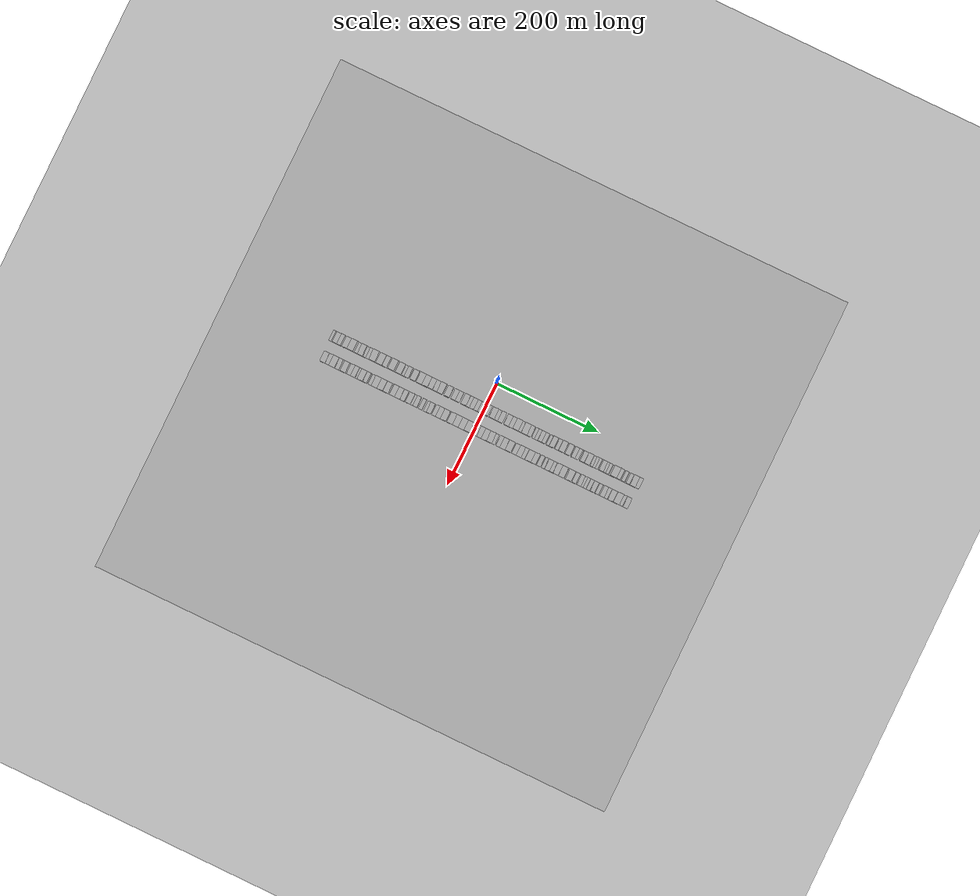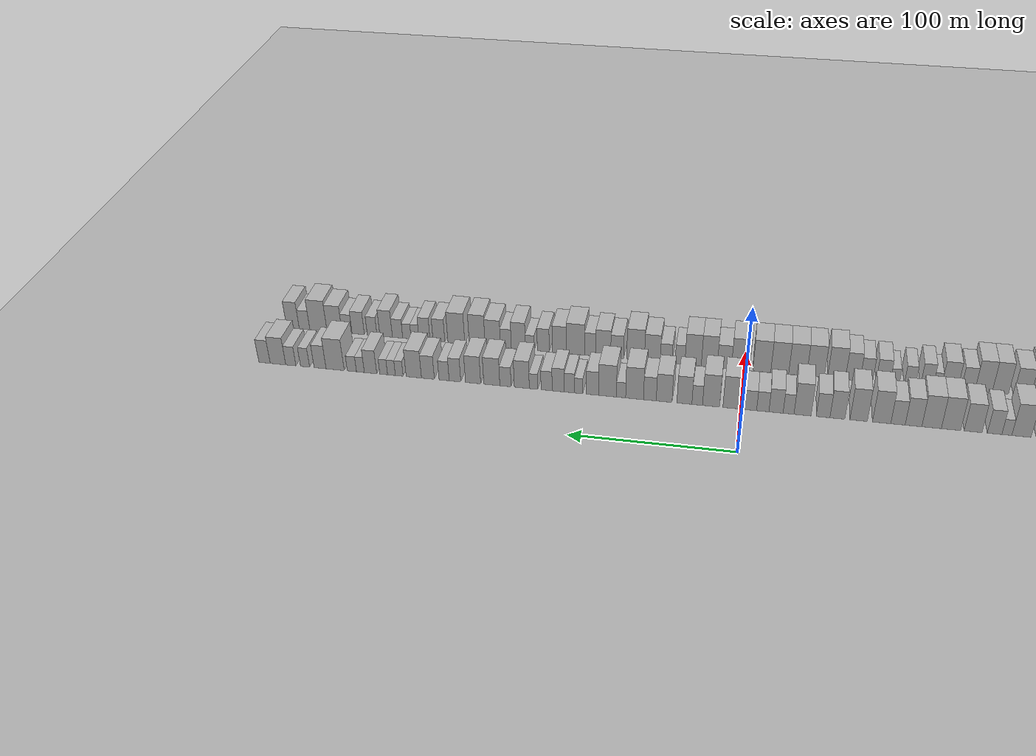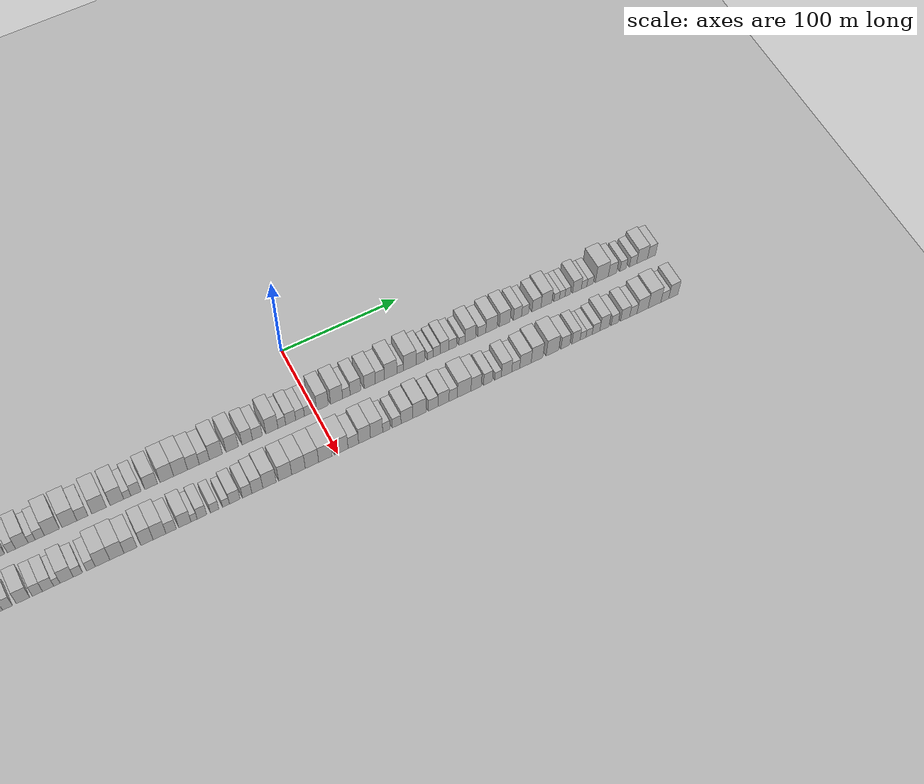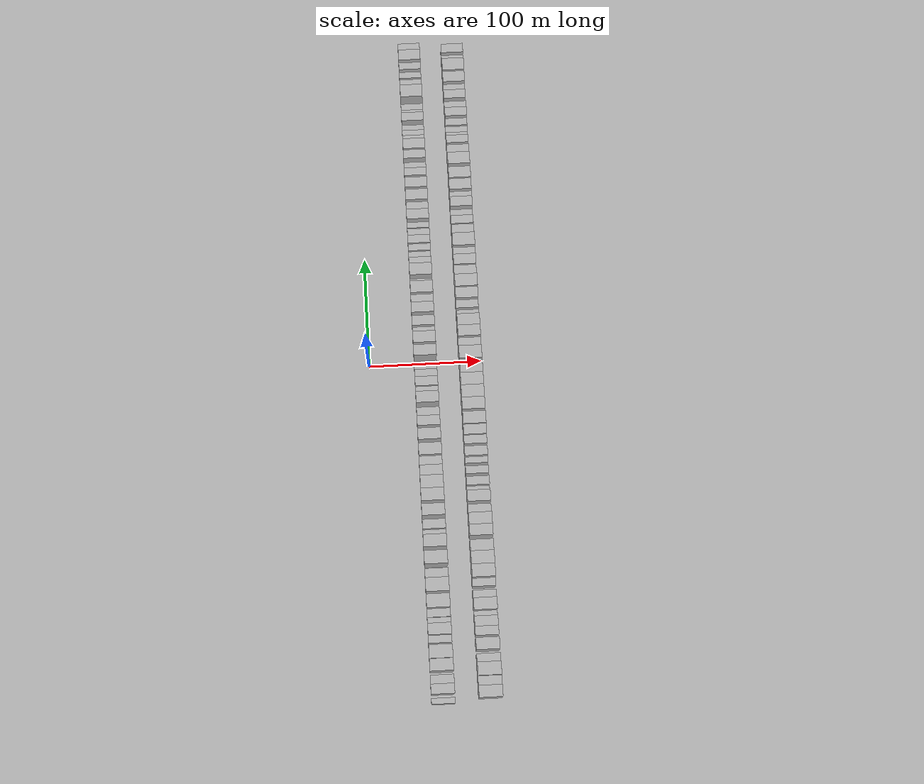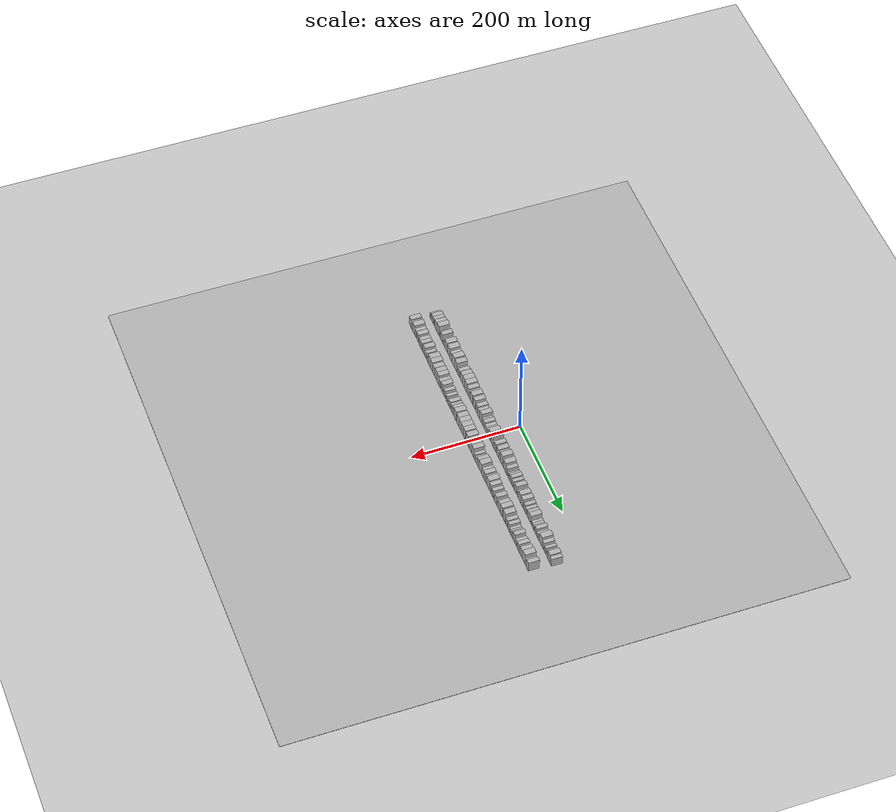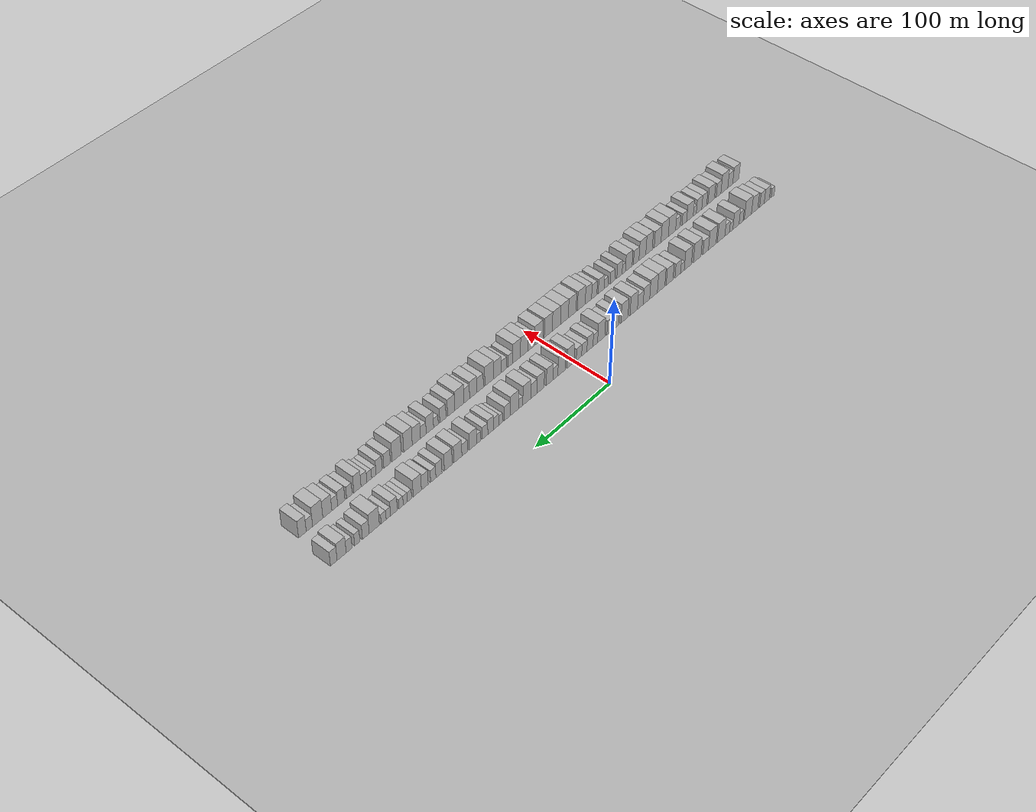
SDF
<?xml version="1.0" encoding="utf-8"?>

<sdf version="1.6">

   <world name="default">

      <gui fullscreen="0">

         <camera name="user_camera">

            <pose>-15 0 4.57585 0 0 0</pose>

            <view_controller>orbit</view_controller>

         </camera>

      </gui>

      <scene>

         <sky>

           <clouds>

             <speed>12</speed>

           </clouds>

         </sky>

         <ambient>0.4 0.4 0.4 1</ambient>

         <background>0.7 0.7 0.7 1</background>

         <shadows>1</shadows>

      </scene>

      <gravity>0 0 -9.8066</gravity>

      <magnetic_field>6e-06 2.3e-05 -4.2e-05</magnetic_field>

      <physics default="0" name="default_physics" type="ode">

         <ode>

            <solver>

               <type>quick</type>

               <iters>10</iters>

               <sor>1.0</sor>

               <use_dynamic_moi_rescaling>0</use_dynamic_moi_rescaling>

            </solver>

            <constraints>

               <cfm>0</cfm>

               <erp>0.2</erp>

               <contact_max_correcting_vel>100</contact_max_correcting_vel>

               <contact_surface_layer>0.001</contact_surface_layer>

            </constraints>

         </ode>

         <max_step_size>0.004</max_step_size>

         <real_time_factor>1</real_time_factor>

         <real_time_update_rate>250</real_time_update_rate>

      </physics>

      <light name="sun" type="directional">

         <cast_shadows>1</cast_shadows>

         <pose>0 0 10 0 0 0</pose>

         <diffuse>0.8 0.8 0.8 1</diffuse>

         <specular>0.2 0.2 0.2 1</specular>

         <attenuation>

            <range>1000</range>

            <constant>0.9</constant>

            <linear>0.01</linear>

            <quadratic>0.001</quadratic>

         </attenuation>

         <direction>-0.5 0.1 -0.9</direction>

      </light>

      <include>

         <name>ground_plane_1</name>

         <uri>model://HANNAS_ground_plane</uri>

         <pose>0 0 0  0 0 0</pose>

      </include>

      <include>

         <name>ground_plane_2</name>

         <uri>model://HANNAS_ground_plane</uri>

         <pose>100 0 0  0 0 0</pose>

      </include>

      <model name="building_1">

         <static>1</static>

         <pose frame="">50.0000 -297.5331 0 0.000000 0.000000 0.000000</pose>

         <link name="link">

            <pose frame="">0 0 6.00 0 0 0</pose>

            <collision name="collision">

               <geometry>

                  <box>

                     <size>20.0000 4.9339 12.0000</size>

                  </box>

               </geometry>

               <max_contacts>10</max_contacts>

               <surface>

                  <contact>

                     <ode/>

                  </contact>

                  <bounce/>

                  <friction>

                     <torsional>

                        <ode/>

                     </torsional>

                     <ode/>

                  </friction>

               </surface>

            </collision>

            <visual name="visual">

               <cast_shadows>0</cast_shadows>

               <geometry>

                  <box>

                     <size>20.0000 4.9339 12.0000</size>

                  </box>

               </geometry>

               <material>

                  <script>

                     <uri>model://HANNAS_wall/materials/scripts</uri>

                     <uri>model://HANNAS_wall/materials/textures</uri>

                     <name>vrc/HANNAS_wall</name>

                  </script>

               </material>

            </visual>

            <self_collide>0</self_collide>

            <enable_wind>0</enable_wind>

            <kinematic>0</kinematic>

         </link>

      </model>

      <model name="building_2">

         <static>1</static>

         <pose frame="">50.0000 -287.8337 0 0.000000 0.000000 0.000000</pose>

         <link name="link">

            <pose frame="">0 0 9.00 0 0 0</pose>

            <collision name="collision">

               <geometry>

                  <box>

                     <size>20.0000 8.4648 18.0000</size>

                  </box>

               </geometry>

               <max_contacts>10</max_contacts>

               <surface>

                  <contact>

                     <ode/>

                  </contact>

                  <bounce/>

                  <friction>

                     <torsional>

                        <ode/>

                     </torsional>

                     <ode/>

                  </friction>

               </surface>

            </collision>

            <visual name="visual">

               <cast_shadows>0</cast_shadows>

               <geometry>

                  <box>

                     <size>20.0000 8.4648 18.0000</size>

                  </box>

               </geometry>

               <material>

                  <script>

                     <uri>model://HANNAS_wall/materials/scripts</uri>

                     <uri>model://HANNAS_wall/materials/textures</uri>

                     <name>vrc/HANNAS_wall</name>

                  </script>

               </material>

            </visual>

            <self_collide>0</self_collide>

            <enable_wind>0</enable_wind>

            <kinematic>0</kinematic>

         </link>

      </model>

      <model name="building_3">

         <static>1</static>

         <pose frame="">50.0000 -279.8977 0 0.000000 0.000000 0.000000</pose>

         <link name="link">

            <pose frame="">0 0 9.00 0 0 0</pose>

            <collision name="collision">

               <geometry>

                  <box>

                     <size>20.0000 7.4073 18.0000</size>

                  </box>

               </geometry>

               <max_contacts>10</max_contacts>

               <surface>

                  <contact>

                     <ode/>

                  </contact>

                  <bounce/>

                  <friction>

                     <torsional>

                        <ode/>

                     </torsional>

                     <ode/>

                  </friction>

               </surface>

            </collision>

            <visual name="visual">

               <cast_shadows>0</cast_shadows>

               <geometry>

                  <box>

                     <size>20.0000 7.4073 18.0000</size>

                  </box>

               </geometry>

               <material>

                  <script>

                     <uri>model://HANNAS_wall/materials/scripts</uri>

                     <uri>model://HANNAS_wall/materials/textures</uri>

                     <name>vrc/HANNAS_wall</name>

                  </script>

               </material>

            </visual>

            <self_collide>0</self_collide>

            <enable_wind>0</enable_wind>

            <kinematic>0</kinematic>

         </link>

      </model>

      <model name="building_4">

         <static>1</static>

         <pose frame="">50.0000 -268.0133 0 0.000000 0.000000 0.000000</pose>

         <link name="link">

            <pose frame="">0 0 10.50 0 0 0</pose>

            <collision name="collision">

               <geometry>

                  <box>

                     <size>20.0000 10.3615 21.0000</size>

                  </box>

               </geometry>

               <max_contacts>10</max_contacts>

               <surface>

                  <contact>

                     <ode/>

                  </contact>

                  <bounce/>

                  <friction>

                     <torsional>

                        <ode/>

                     </torsional>

                     <ode/>

                  </friction>

               </surface>

            </collision>

            <visual name="visual">

               <cast_shadows>0</cast_shadows>

               <geometry>

                  <box>

                     <size>20.0000 10.3615 21.0000</size>

                  </box>

               </geometry>

               <material>

                  <script>

                     <uri>model://HANNAS_wall/materials/scripts</uri>

                     <uri>model://HANNAS_wall/materials/textures</uri>

                     <name>vrc/HANNAS_wall</name>

                  </script>

               </material>

            </visual>

            <self_collide>0</self_collide>

            <enable_wind>0</enable_wind>

            <kinematic>0</kinematic>

         </link>

      </model>

      <model name="building_5">

         <static>1</static>

         <pose frame="">50.0000 -257.1095 0 0.000000 0.000000 0.000000</pose>

         <link name="link">

            <pose frame="">0 0 12.00 0 0 0</pose>

            <collision name="collision">

               <geometry>

                  <box>

                     <size>20.0000 11.4461 24.0000</size>

                  </box>

               </geometry>

               <max_contacts>10</max_contacts>

               <surface>

                  <contact>

                     <ode/>

                  </contact>

                  <bounce/>

                  <friction>

                     <torsional>

                        <ode/>

                     </torsional>

                     <ode/>

                  </friction>

               </surface>

            </collision>

            <visual name="visual">

               <cast_shadows>0</cast_shadows>

               <geometry>

                  <box>

                     <size>20.0000 11.4461 24.0000</size>

                  </box>

               </geometry>

               <material>

                  <script>

                     <uri>model://HANNAS_wall/materials/scripts</uri>

                     <uri>model://HANNAS_wall/materials/textures</uri>

                     <name>vrc/HANNAS_wall</name>

                  </script>

               </material>

            </visual>

            <self_collide>0</self_collide>

            <enable_wind>0</enable_wind>

            <kinematic>0</kinematic>

         </link>

      </model>

      <model name="building_6">

         <static>1</static>

         <pose frame="">50.0000 -246.1366 0 0.000000 0.000000 0.000000</pose>

         <link name="link">

            <pose frame="">0 0 7.50 0 0 0</pose>

            <collision name="collision">

               <geometry>

                  <box>

                     <size>20.0000 6.4996 15.0000</size>

                  </box>

               </geometry>

               <max_contacts>10</max_contacts>

               <surface>

                  <contact>

                     <ode/>

                  </contact>

                  <bounce/>

                  <friction>

                     <torsional>

                        <ode/>

                     </torsional>

                     <ode/>

                  </friction>

               </surface>

            </collision>

            <visual name="visual">

               <cast_shadows>0</cast_shadows>

               <geometry>

                  <box>

                     <size>20.0000 6.4996 15.0000</size>

                  </box>

               </geometry>

               <material>

                  <script>

                     <uri>model://HANNAS_wall/materials/scripts</uri>

                     <uri>model://HANNAS_wall/materials/textures</uri>

                     <name>vrc/HANNAS_wall</name>

                  </script>

               </material>

            </visual>

            <self_collide>0</self_collide>

            <enable_wind>0</enable_wind>

            <kinematic>0</kinematic>

         </link>

      </model>

      <model name="building_7">

         <static>1</static>

         <pose frame="">50.0000 -237.9815 0 0.000000 0.000000 0.000000</pose>

         <link name="link">

            <pose frame="">0 0 10.50 0 0 0</pose>

            <collision name="collision">

               <geometry>

                  <box>

                     <size>20.0000 9.8106 21.0000</size>

                  </box>

               </geometry>

               <max_contacts>10</max_contacts>

               <surface>

                  <contact>

                     <ode/>

                  </contact>

                  <bounce/>

                  <friction>

                     <torsional>

                        <ode/>

                     </torsional>

                     <ode/>

                  </friction>

               </surface>

            </collision>

            <visual name="visual">

               <cast_shadows>0</cast_shadows>

               <geometry>

                  <box>

                     <size>20.0000 9.8106 21.0000</size>

                  </box>

               </geometry>

               <material>

                  <script>

                     <uri>model://HANNAS_wall/materials/scripts</uri>

                     <uri>model://HANNAS_wall/materials/textures</uri>

                     <name>vrc/HANNAS_wall</name>

                  </script>

               </material>

            </visual>

            <self_collide>0</self_collide>

            <enable_wind>0</enable_wind>

            <kinematic>0</kinematic>

         </link>

      </model>

      <model name="building_8">

         <static>1</static>

         <pose frame="">50.0000 -230.3521 0 0.000000 0.000000 0.000000</pose>

         <link name="link">

            <pose frame="">0 0 6.00 0 0 0</pose>

            <collision name="collision">

               <geometry>

                  <box>

                     <size>20.0000 5.4483 12.0000</size>

                  </box>

               </geometry>

               <max_contacts>10</max_contacts>

               <surface>

                  <contact>

                     <ode/>

                  </contact>

                  <bounce/>

                  <friction>

                     <torsional>

                        <ode/>

                     </torsional>

                     <ode/>

                  </friction>

               </surface>

            </collision>

            <visual name="visual">

               <cast_shadows>0</cast_shadows>

               <geometry>

                  <box>

                     <size>20.0000 5.4483 12.0000</size>

                  </box>

               </geometry>

               <material>

                  <script>

                     <uri>model://HANNAS_wall/materials/scripts</uri>

                     <uri>model://HANNAS_wall/materials/textures</uri>

                     <name>vrc/HANNAS_wall</name>

                  </script>

               </material>

            </visual>

            <self_collide>0</self_collide>

            <enable_wind>0</enable_wind>

            <kinematic>0</kinematic>

         </link>

      </model>

      <model name="building_9">

         <static>1</static>

         <pose frame="">50.0000 -224.0166 0 0.000000 0.000000 0.000000</pose>

         <link name="link">

            <pose frame="">0 0 7.50 0 0 0</pose>

            <collision name="collision">

               <geometry>

                  <box>

                     <size>20.0000 7.2227 15.0000</size>

                  </box>

               </geometry>

               <max_contacts>10</max_contacts>

               <surface>

                  <contact>

                     <ode/>

                  </contact>

                  <bounce/>

                  <friction>

                     <torsional>

                        <ode/>

                     </torsional>

                     <ode/>

                  </friction>

               </surface>

            </collision>

            <visual name="visual">

               <cast_shadows>0</cast_shadows>

               <geometry>

                  <box>

                     <size>20.0000 7.2227 15.0000</size>

                  </box>

               </geometry>

               <material>

                  <script>

                     <uri>model://HANNAS_wall/materials/scripts</uri>

                     <uri>model://HANNAS_wall/materials/textures</uri>

                     <name>vrc/HANNAS_wall</name>

                  </script>

               </material>

            </visual>

            <self_collide>0</self_collide>

            <enable_wind>0</enable_wind>

            <kinematic>0</kinematic>

         </link>

      </model>

      <model name="building_10">

         <static>1</static>

         <pose frame="">50.0000 -214.5583 0 0.000000 0.000000 0.000000</pose>

         <link name="link">

            <pose frame="">0 0 12.00 0 0 0</pose>

            <collision name="collision">

               <geometry>

                  <box>

                     <size>20.0000 11.6939 24.0000</size>

                  </box>

               </geometry>

               <max_contacts>10</max_contacts>

               <surface>

                  <contact>

                     <ode/>

                  </contact>

                  <bounce/>

                  <friction>

                     <torsional>

                        <ode/>

                     </torsional>

                     <ode/>

                  </friction>

               </surface>

            </collision>

            <visual name="visual">

               <cast_shadows>0</cast_shadows>

               <geometry>

                  <box>

                     <size>20.0000 11.6939 24.0000</size>

                  </box>

               </geometry>

               <material>

                  <script>

                     <uri>model://HANNAS_wall/materials/scripts</uri>

                     <uri>model://HANNAS_wall/materials/textures</uri>

                     <name>vrc/HANNAS_wall</name>

                  </script>

               </material>

            </visual>

            <self_collide>0</self_collide>

            <enable_wind>0</enable_wind>

            <kinematic>0</kinematic>

         </link>

      </model>

      <model name="building_11">

         <static>1</static>

         <pose frame="">50.0000 -200.7927 0 0.000000 0.000000 0.000000</pose>

         <link name="link">

            <pose frame="">0 0 12.00 0 0 0</pose>

            <collision name="collision">

               <geometry>

                  <box>

                     <size>20.0000 11.8374 24.0000</size>

                  </box>

               </geometry>

               <max_contacts>10</max_contacts>

               <surface>

                  <contact>

                     <ode/>

                  </contact>

                  <bounce/>

                  <friction>

                     <torsional>

                        <ode/>

                     </torsional>

                     <ode/>

                  </friction>

               </surface>

            </collision>

            <visual name="visual">

               <cast_shadows>0</cast_shadows>

               <geometry>

                  <box>

                     <size>20.0000 11.8374 24.0000</size>

                  </box>

               </geometry>

               <material>

                  <script>

                     <uri>model://HANNAS_wall/materials/scripts</uri>

                     <uri>model://HANNAS_wall/materials/textures</uri>

                     <name>vrc/HANNAS_wall</name>

                  </script>

               </material>

            </visual>

            <self_collide>0</self_collide>

            <enable_wind>0</enable_wind>

            <kinematic>0</kinematic>

         </link>

      </model>

      <model name="building_12">

         <static>1</static>

         <pose frame="">50.0000 -190.5478 0 0.000000 0.000000 0.000000</pose>

         <link name="link">

            <pose frame="">0 0 9.00 0 0 0</pose>

            <collision name="collision">

               <geometry>

                  <box>

                     <size>20.0000 8.6524 18.0000</size>

                  </box>

               </geometry>

               <max_contacts>10</max_contacts>

               <surface>

                  <contact>

                     <ode/>

                  </contact>

                  <bounce/>

                  <friction>

                     <torsional>

                        <ode/>

                     </torsional>

                     <ode/>

                  </friction>

               </surface>

            </collision>

            <visual name="visual">

               <cast_shadows>0</cast_shadows>

               <geometry>

                  <box>

                     <size>20.0000 8.6524 18.0000</size>

                  </box>

               </geometry>

               <material>

                  <script>

                     <uri>model://HANNAS_wall/materials/scripts</uri>

                     <uri>model://HANNAS_wall/materials/textures</uri>

                     <name>vrc/HANNAS_wall</name>

                  </script>

               </material>

            </visual>

            <self_collide>0</self_collide>

            <enable_wind>0</enable_wind>

            <kinematic>0</kinematic>

         </link>

      </model>

      <model name="building_13">

         <static>1</static>

         <pose frame="">50.0000 -177.4273 0 0.000000 0.000000 0.000000</pose>

         <link name="link">

            <pose frame="">0 0 12.00 0 0 0</pose>

            <collision name="collision">

               <geometry>

                  <box>

                     <size>20.0000 11.5886 24.0000</size>

                  </box>

               </geometry>

               <max_contacts>10</max_contacts>

               <surface>

                  <contact>

                     <ode/>

                  </contact>

                  <bounce/>

                  <friction>

                     <torsional>

                        <ode/>

                     </torsional>

                     <ode/>

                  </friction>

               </surface>

            </collision>

            <visual name="visual">

               <cast_shadows>0</cast_shadows>

               <geometry>

                  <box>

                     <size>20.0000 11.5886 24.0000</size>

                  </box>

               </geometry>

               <material>

                  <script>

                     <uri>model://HANNAS_wall/materials/scripts</uri>

                     <uri>model://HANNAS_wall/materials/textures</uri>

                     <name>vrc/HANNAS_wall</name>

                  </script>

               </material>

            </visual>

            <self_collide>0</self_collide>

            <enable_wind>0</enable_wind>

            <kinematic>0</kinematic>

         </link>

      </model>

      <model name="building_14">

         <static>1</static>

         <pose frame="">50.0000 -163.1958 0 0.000000 0.000000 0.000000</pose>

         <link name="link">

            <pose frame="">0 0 12.00 0 0 0</pose>

            <collision name="collision">

               <geometry>

                  <box>

                     <size>20.0000 10.8744 24.0000</size>

                  </box>

               </geometry>

               <max_contacts>10</max_contacts>

               <surface>

                  <contact>

                     <ode/>

                  </contact>

                  <bounce/>

                  <friction>

                     <torsional>

                        <ode/>

                     </torsional>

                     <ode/>

                  </friction>

               </surface>

            </collision>

            <visual name="visual">

               <cast_shadows>0</cast_shadows>

               <geometry>

                  <box>

                     <size>20.0000 10.8744 24.0000</size>

                  </box>

               </geometry>

               <material>

                  <script>

                     <uri>model://HANNAS_wall/materials/scripts</uri>

                     <uri>model://HANNAS_wall/materials/textures</uri>

                     <name>vrc/HANNAS_wall</name>

                  </script>

               </material>

            </visual>

            <self_collide>0</self_collide>

            <enable_wind>0</enable_wind>

            <kinematic>0</kinematic>

         </link>

      </model>

      <model name="building_15">

         <static>1</static>

         <pose frame="">50.0000 -154.9076 0 0.000000 0.000000 0.000000</pose>

         <link name="link">

            <pose frame="">0 0 6.00 0 0 0</pose>

            <collision name="collision">

               <geometry>

                  <box>

                     <size>20.0000 5.7019 12.0000</size>

                  </box>

               </geometry>

               <max_contacts>10</max_contacts>

               <surface>

                  <contact>

                     <ode/>

                  </contact>

                  <bounce/>

                  <friction>

                     <torsional>

                        <ode/>

                     </torsional>

                     <ode/>

                  </friction>

               </surface>

            </collision>

            <visual name="visual">

               <cast_shadows>0</cast_shadows>

               <geometry>

                  <box>

                     <size>20.0000 5.7019 12.0000</size>

                  </box>

               </geometry>

               <material>

                  <script>

                     <uri>model://HANNAS_wall/materials/scripts</uri>

                     <uri>model://HANNAS_wall/materials/textures</uri>

                     <name>vrc/HANNAS_wall</name>

                  </script>

               </material>

            </visual>

            <self_collide>0</self_collide>

            <enable_wind>0</enable_wind>

            <kinematic>0</kinematic>

         </link>

      </model>

      <model name="building_16">

         <static>1</static>

         <pose frame="">50.0000 -147.9186 0 0.000000 0.000000 0.000000</pose>

         <link name="link">

            <pose frame="">0 0 9.00 0 0 0</pose>

            <collision name="collision">

               <geometry>

                  <box>

                     <size>20.0000 8.2761 18.0000</size>

                  </box>

               </geometry>

               <max_contacts>10</max_contacts>

               <surface>

                  <contact>

                     <ode/>

                  </contact>

                  <bounce/>

                  <friction>

                     <torsional>

                        <ode/>

                     </torsional>

                     <ode/>

                  </friction>

               </surface>

            </collision>

            <visual name="visual">

               <cast_shadows>0</cast_shadows>

               <geometry>

                  <box>

                     <size>20.0000 8.2761 18.0000</size>

                  </box>

               </geometry>

               <material>

                  <script>

                     <uri>model://HANNAS_wall/materials/scripts</uri>

                     <uri>model://HANNAS_wall/materials/textures</uri>

                     <name>vrc/HANNAS_wall</name>

                  </script>

               </material>

            </visual>

            <self_collide>0</self_collide>

            <enable_wind>0</enable_wind>

            <kinematic>0</kinematic>

         </link>

      </model>

      <model name="building_17">

         <static>1</static>

         <pose frame="">50.0000 -135.6512 0 0.000000 0.000000 0.000000</pose>

         <link name="link">

            <pose frame="">0 0 10.50 0 0 0</pose>

            <collision name="collision">

               <geometry>

                  <box>

                     <size>20.0000 10.2588 21.0000</size>

                  </box>

               </geometry>

               <max_contacts>10</max_contacts>

               <surface>

                  <contact>

                     <ode/>

                  </contact>

                  <bounce/>

                  <friction>

                     <torsional>

                        <ode/>

                     </torsional>

                     <ode/>

                  </friction>

               </surface>

            </collision>

            <visual name="visual">

               <cast_shadows>0</cast_shadows>

               <geometry>

                  <box>

                     <size>20.0000 10.2588 21.0000</size>

                  </box>

               </geometry>

               <material>

                  <script>

                     <uri>model://HANNAS_wall/materials/scripts</uri>

                     <uri>model://HANNAS_wall/materials/textures</uri>

                     <name>vrc/HANNAS_wall</name>

                  </script>

               </material>

            </visual>

            <self_collide>0</self_collide>

            <enable_wind>0</enable_wind>

            <kinematic>0</kinematic>

         </link>

      </model>

      <model name="building_18">

         <static>1</static>

         <pose frame="">50.0000 -122.9784 0 0.000000 0.000000 0.000000</pose>

         <link name="link">

            <pose frame="">0 0 12.00 0 0 0</pose>

            <collision name="collision">

               <geometry>

                  <box>

                     <size>20.0000 11.0869 24.0000</size>

                  </box>

               </geometry>

               <max_contacts>10</max_contacts>

               <surface>

                  <contact>

                     <ode/>

                  </contact>

                  <bounce/>

                  <friction>

                     <torsional>

                        <ode/>

                     </torsional>

                     <ode/>

                  </friction>

               </surface>

            </collision>

            <visual name="visual">

               <cast_shadows>0</cast_shadows>

               <geometry>

                  <box>

                     <size>20.0000 11.0869 24.0000</size>

                  </box>

               </geometry>

               <material>

                  <script>

                     <uri>model://HANNAS_wall/materials/scripts</uri>

                     <uri>model://HANNAS_wall/materials/textures</uri>

                     <name>vrc/HANNAS_wall</name>

                  </script>

               </material>

            </visual>

            <self_collide>0</self_collide>

            <enable_wind>0</enable_wind>

            <kinematic>0</kinematic>

         </link>

      </model>

      <model name="building_19">

         <static>1</static>

         <pose frame="">50.0000 -111.7870 0 0.000000 0.000000 0.000000</pose>

         <link name="link">

            <pose frame="">0 0 12.00 0 0 0</pose>

            <collision name="collision">

               <geometry>

                  <box>

                     <size>20.0000 11.2959 24.0000</size>

                  </box>

               </geometry>

               <max_contacts>10</max_contacts>

               <surface>

                  <contact>

                     <ode/>

                  </contact>

                  <bounce/>

                  <friction>

                     <torsional>

                        <ode/>

                     </torsional>

                     <ode/>

                  </friction>

               </surface>

            </collision>

            <visual name="visual">

               <cast_shadows>0</cast_shadows>

               <geometry>

                  <box>

                     <size>20.0000 11.2959 24.0000</size>

                  </box>

               </geometry>

               <material>

                  <script>

                     <uri>model://HANNAS_wall/materials/scripts</uri>

                     <uri>model://HANNAS_wall/materials/textures</uri>

                     <name>vrc/HANNAS_wall</name>

                  </script>

               </material>

            </visual>

            <self_collide>0</self_collide>

            <enable_wind>0</enable_wind>

            <kinematic>0</kinematic>

         </link>

      </model>

      <model name="building_20">

         <static>1</static>

         <pose frame="">50.0000 -101.3249 0 0.000000 0.000000 0.000000</pose>

         <link name="link">

            <pose frame="">0 0 10.50 0 0 0</pose>

            <collision name="collision">

               <geometry>

                  <box>

                     <size>20.0000 9.6283 21.0000</size>

                  </box>

               </geometry>

               <max_contacts>10</max_contacts>

               <surface>

                  <contact>

                     <ode/>

                  </contact>

                  <bounce/>

                  <friction>

                     <torsional>

                        <ode/>

                     </torsional>

                     <ode/>

                  </friction>

               </surface>

            </collision>

            <visual name="visual">

               <cast_shadows>0</cast_shadows>

               <geometry>

                  <box>

                     <size>20.0000 9.6283 21.0000</size>

                  </box>

               </geometry>

               <material>

                  <script>

                     <uri>model://HANNAS_wall/materials/scripts</uri>

                     <uri>model://HANNAS_wall/materials/textures</uri>

                     <name>vrc/HANNAS_wall</name>

                  </script>

               </material>

            </visual>

            <self_collide>0</self_collide>

            <enable_wind>0</enable_wind>

            <kinematic>0</kinematic>

         </link>

      </model>

      <model name="building_21">

         <static>1</static>

         <pose frame="">50.0000 -92.3364 0 0.000000 0.000000 0.000000</pose>

         <link name="link">

            <pose frame="">0 0 9.00 0 0 0</pose>

            <collision name="collision">

               <geometry>

                  <box>

                     <size>20.0000 8.3488 18.0000</size>

                  </box>

               </geometry>

               <max_contacts>10</max_contacts>

               <surface>

                  <contact>

                     <ode/>

                  </contact>

                  <bounce/>

                  <friction>

                     <torsional>

                        <ode/>

                     </torsional>

                     <ode/>

                  </friction>

               </surface>

            </collision>

            <visual name="visual">

               <cast_shadows>0</cast_shadows>

               <geometry>

                  <box>

                     <size>20.0000 8.3488 18.0000</size>

                  </box>

               </geometry>

               <material>

                  <script>

                     <uri>model://HANNAS_wall/materials/scripts</uri>

                     <uri>model://HANNAS_wall/materials/textures</uri>

                     <name>vrc/HANNAS_wall</name>

                  </script>

               </material>

            </visual>

            <self_collide>0</self_collide>

            <enable_wind>0</enable_wind>

            <kinematic>0</kinematic>

         </link>

      </model>

      <model name="building_22">

         <static>1</static>

         <pose frame="">50.0000 -82.8064 0 0.000000 0.000000 0.000000</pose>

         <link name="link">

            <pose frame="">0 0 12.00 0 0 0</pose>

            <collision name="collision">

               <geometry>

                  <box>

                     <size>20.0000 10.7113 24.0000</size>

                  </box>

               </geometry>

               <max_contacts>10</max_contacts>

               <surface>

                  <contact>

                     <ode/>

                  </contact>

                  <bounce/>

                  <friction>

                     <torsional>

                        <ode/>

                     </torsional>

                     <ode/>

                  </friction>

               </surface>

            </collision>

            <visual name="visual">

               <cast_shadows>0</cast_shadows>

               <geometry>

                  <box>

                     <size>20.0000 10.7113 24.0000</size>

                  </box>

               </geometry>

               <material>

                  <script>

                     <uri>model://HANNAS_wall/materials/scripts</uri>

                     <uri>model://HANNAS_wall/materials/textures</uri>

                     <name>vrc/HANNAS_wall</name>

                  </script>

               </material>

            </visual>

            <self_collide>0</self_collide>

            <enable_wind>0</enable_wind>

            <kinematic>0</kinematic>

         </link>

      </model>

      <model name="building_23">

         <static>1</static>

         <pose frame="">50.0000 -69.3587 0 0.000000 0.000000 0.000000</pose>

         <link name="link">

            <pose frame="">0 0 12.00 0 0 0</pose>

            <collision name="collision">

               <geometry>

                  <box>

                     <size>20.0000 10.1841 24.0000</size>

                  </box>

               </geometry>

               <max_contacts>10</max_contacts>

               <surface>

                  <contact>

                     <ode/>

                  </contact>

                  <bounce/>

                  <friction>

                     <torsional>

                        <ode/>

                     </torsional>

                     <ode/>

                  </friction>

               </surface>

            </collision>

            <visual name="visual">

               <cast_shadows>0</cast_shadows>

               <geometry>

                  <box>

                     <size>20.0000 10.1841 24.0000</size>

                  </box>

               </geometry>

               <material>

                  <script>

                     <uri>model://HANNAS_wall/materials/scripts</uri>

                     <uri>model://HANNAS_wall/materials/textures</uri>

                     <name>vrc/HANNAS_wall</name>

                  </script>

               </material>

            </visual>

            <self_collide>0</self_collide>

            <enable_wind>0</enable_wind>

            <kinematic>0</kinematic>

         </link>

      </model>

      <model name="building_24">

         <static>1</static>

         <pose frame="">50.0000 -56.8853 0 0.000000 0.000000 0.000000</pose>

         <link name="link">

            <pose frame="">0 0 10.50 0 0 0</pose>

            <collision name="collision">

               <geometry>

                  <box>

                     <size>20.0000 8.7627 21.0000</size>

                  </box>

               </geometry>

               <max_contacts>10</max_contacts>

               <surface>

                  <contact>

                     <ode/>

                  </contact>

                  <bounce/>

                  <friction>

                     <torsional>

                        <ode/>

                     </torsional>

                     <ode/>

                  </friction>

               </surface>

            </collision>

            <visual name="visual">

               <cast_shadows>0</cast_shadows>

               <geometry>

                  <box>

                     <size>20.0000 8.7627 21.0000</size>

                  </box>

               </geometry>

               <material>

                  <script>

                     <uri>model://HANNAS_wall/materials/scripts</uri>

                     <uri>model://HANNAS_wall/materials/textures</uri>

                     <name>vrc/HANNAS_wall</name>

                  </script>

               </material>

            </visual>

            <self_collide>0</self_collide>

            <enable_wind>0</enable_wind>

            <kinematic>0</kinematic>

         </link>

      </model>

      <model name="building_25">

         <static>1</static>

         <pose frame="">50.0000 -48.4280 0 0.000000 0.000000 0.000000</pose>

         <link name="link">

            <pose frame="">0 0 9.00 0 0 0</pose>

            <collision name="collision">

               <geometry>

                  <box>

                     <size>20.0000 8.1518 18.0000</size>

                  </box>

               </geometry>

               <max_contacts>10</max_contacts>

               <surface>

                  <contact>

                     <ode/>

                  </contact>

                  <bounce/>

                  <friction>

                     <torsional>

                        <ode/>

                     </torsional>

                     <ode/>

                  </friction>

               </surface>

            </collision>

            <visual name="visual">

               <cast_shadows>0</cast_shadows>

               <geometry>

                  <box>

                     <size>20.0000 8.1518 18.0000</size>

                  </box>

               </geometry>

               <material>

                  <script>

                     <uri>model://HANNAS_wall/materials/scripts</uri>

                     <uri>model://HANNAS_wall/materials/textures</uri>

                     <name>vrc/HANNAS_wall</name>

                  </script>

               </material>

            </visual>

            <self_collide>0</self_collide>

            <enable_wind>0</enable_wind>

            <kinematic>0</kinematic>

         </link>

      </model>

      <model name="building_26">

         <static>1</static>

         <pose frame="">50.0000 -36.2777 0 0.000000 0.000000 0.000000</pose>

         <link name="link">

            <pose frame="">0 0 12.00 0 0 0</pose>

            <collision name="collision">

               <geometry>

                  <box>

                     <size>20.0000 10.1488 24.0000</size>

                  </box>

               </geometry>

               <max_contacts>10</max_contacts>

               <surface>

                  <contact>

                     <ode/>

                  </contact>

                  <bounce/>

                  <friction>

                     <torsional>

                        <ode/>

                     </torsional>

                     <ode/>

                  </friction>

               </surface>

            </collision>

            <visual name="visual">

               <cast_shadows>0</cast_shadows>

               <geometry>

                  <box>

                     <size>20.0000 10.1488 24.0000</size>

                  </box>

               </geometry>

               <material>

                  <script>

                     <uri>model://HANNAS_wall/materials/scripts</uri>

                     <uri>model://HANNAS_wall/materials/textures</uri>

                     <name>vrc/HANNAS_wall</name>

                  </script>

               </material>

            </visual>

            <self_collide>0</self_collide>

            <enable_wind>0</enable_wind>

            <kinematic>0</kinematic>

         </link>

      </model>

      <model name="building_27">

         <static>1</static>

         <pose frame="">50.0000 -27.9706 0 0.000000 0.000000 0.000000</pose>

         <link name="link">

            <pose frame="">0 0 7.50 0 0 0</pose>

            <collision name="collision">

               <geometry>

                  <box>

                     <size>20.0000 6.4655 15.0000</size>

                  </box>

               </geometry>

               <max_contacts>10</max_contacts>

               <surface>

                  <contact>

                     <ode/>

                  </contact>

                  <bounce/>

                  <friction>

                     <torsional>

                        <ode/>

                     </torsional>

                     <ode/>

                  </friction>

               </surface>

            </collision>

            <visual name="visual">

               <cast_shadows>0</cast_shadows>

               <geometry>

                  <box>

                     <size>20.0000 6.4655 15.0000</size>

                  </box>

               </geometry>

               <material>

                  <script>

                     <uri>model://HANNAS_wall/materials/scripts</uri>

                     <uri>model://HANNAS_wall/materials/textures</uri>

                     <name>vrc/HANNAS_wall</name>

                  </script>

               </material>

            </visual>

            <self_collide>0</self_collide>

            <enable_wind>0</enable_wind>

            <kinematic>0</kinematic>

         </link>

      </model>

      <model name="building_28">

         <static>1</static>

         <pose frame="">50.0000 -20.5043 0 0.000000 0.000000 0.000000</pose>

         <link name="link">

            <pose frame="">0 0 9.00 0 0 0</pose>

            <collision name="collision">

               <geometry>

                  <box>

                     <size>20.0000 8.4670 18.0000</size>

                  </box>

               </geometry>

               <max_contacts>10</max_contacts>

               <surface>

                  <contact>

                     <ode/>

                  </contact>

                  <bounce/>

                  <friction>

                     <torsional>

                        <ode/>

                     </torsional>

                     <ode/>

                  </friction>

               </surface>

            </collision>

            <visual name="visual">

               <cast_shadows>0</cast_shadows>

               <geometry>

                  <box>

                     <size>20.0000 8.4670 18.0000</size>

                  </box>

               </geometry>

               <material>

                  <script>

                     <uri>model://HANNAS_wall/materials/scripts</uri>

                     <uri>model://HANNAS_wall/materials/textures</uri>

                     <name>vrc/HANNAS_wall</name>

                  </script>

               </material>

            </visual>

            <self_collide>0</self_collide>

            <enable_wind>0</enable_wind>

            <kinematic>0</kinematic>

         </link>

      </model>

      <model name="building_29">

         <static>1</static>

         <pose frame="">50.0000 -12.5937 0 0.000000 0.000000 0.000000</pose>

         <link name="link">

            <pose frame="">0 0 7.50 0 0 0</pose>

            <collision name="collision">

               <geometry>

                  <box>

                     <size>20.0000 7.3543 15.0000</size>

                  </box>

               </geometry>

               <max_contacts>10</max_contacts>

               <surface>

                  <contact>

                     <ode/>

                  </contact>

                  <bounce/>

                  <friction>

                     <torsional>

                        <ode/>

                     </torsional>

                     <ode/>

                  </friction>

               </surface>

            </collision>

            <visual name="visual">

               <cast_shadows>0</cast_shadows>

               <geometry>

                  <box>

                     <size>20.0000 7.3543 15.0000</size>

                  </box>

               </geometry>

               <material>

                  <script>

                     <uri>model://HANNAS_wall/materials/scripts</uri>

                     <uri>model://HANNAS_wall/materials/textures</uri>

                     <name>vrc/HANNAS_wall</name>

                  </script>

               </material>

            </visual>

            <self_collide>0</self_collide>

            <enable_wind>0</enable_wind>

            <kinematic>0</kinematic>

         </link>

      </model>

      <model name="building_30">

         <static>1</static>

         <pose frame="">50.0000 -5.2264 0 0.000000 0.000000 0.000000</pose>

         <link name="link">

            <pose frame="">0 0 7.50 0 0 0</pose>

            <collision name="collision">

               <geometry>

                  <box>

                     <size>20.0000 7.3801 15.0000</size>

                  </box>

               </geometry>

               <max_contacts>10</max_contacts>

               <surface>

                  <contact>

                     <ode/>

                  </contact>

                  <bounce/>

                  <friction>

                     <torsional>

                        <ode/>

                     </torsional>

                     <ode/>

                  </friction>

               </surface>

            </collision>

            <visual name="visual">

               <cast_shadows>0</cast_shadows>

               <geometry>

                  <box>

                     <size>20.0000 7.3801 15.0000</size>

                  </box>

               </geometry>

               <material>

                  <script>

                     <uri>model://HANNAS_wall/materials/scripts</uri>

                     <uri>model://HANNAS_wall/materials/textures</uri>

                     <name>vrc/HANNAS_wall</name>

                  </script>

               </material>

            </visual>

            <self_collide>0</self_collide>

            <enable_wind>0</enable_wind>

            <kinematic>0</kinematic>

         </link>

      </model>

      <model name="building_31">

         <static>1</static>

         <pose frame="">50.0000 6.4105 0 0.000000 0.000000 0.000000</pose>

         <link name="link">

            <pose frame="">0 0 12.00 0 0 0</pose>

            <collision name="collision">

               <geometry>

                  <box>

                     <size>20.0000 9.8938 24.0000</size>

                  </box>

               </geometry>

               <max_contacts>10</max_contacts>

               <surface>

                  <contact>

                     <ode/>

                  </contact>

                  <bounce/>

                  <friction>

                     <torsional>

                        <ode/>

                     </torsional>

                     <ode/>

                  </friction>

               </surface>

            </collision>

            <visual name="visual">

               <cast_shadows>0</cast_shadows>

               <geometry>

                  <box>

                     <size>20.0000 9.8938 24.0000</size>

                  </box>

               </geometry>

               <material>

                  <script>

                     <uri>model://HANNAS_wall/materials/scripts</uri>

                     <uri>model://HANNAS_wall/materials/textures</uri>

                     <name>vrc/HANNAS_wall</name>

                  </script>

               </material>

            </visual>

            <self_collide>0</self_collide>

            <enable_wind>0</enable_wind>

            <kinematic>0</kinematic>

         </link>

      </model>

      <model name="building_32">

         <static>1</static>

         <pose frame="">50.0000 18.5076 0 0.000000 0.000000 0.000000</pose>

         <link name="link">

            <pose frame="">0 0 12.00 0 0 0</pose>

            <collision name="collision">

               <geometry>

                  <box>

                     <size>20.0000 10.3004 24.0000</size>

                  </box>

               </geometry>

               <max_contacts>10</max_contacts>

               <surface>

                  <contact>

                     <ode/>

                  </contact>

                  <bounce/>

                  <friction>

                     <torsional>

                        <ode/>

                     </torsional>

                     <ode/>

                  </friction>

               </surface>

            </collision>

            <visual name="visual">

               <cast_shadows>0</cast_shadows>

               <geometry>

                  <box>

                     <size>20.0000 10.3004 24.0000</size>

                  </box>

               </geometry>

               <material>

                  <script>

                     <uri>model://HANNAS_wall/materials/scripts</uri>

                     <uri>model://HANNAS_wall/materials/textures</uri>

                     <name>vrc/HANNAS_wall</name>

                  </script>

               </material>

            </visual>

            <self_collide>0</self_collide>

            <enable_wind>0</enable_wind>

            <kinematic>0</kinematic>

         </link>

      </model>

      <model name="building_33">

         <static>1</static>

         <pose frame="">50.0000 26.8743 0 0.000000 0.000000 0.000000</pose>

         <link name="link">

            <pose frame="">0 0 7.50 0 0 0</pose>

            <collision name="collision">

               <geometry>

                  <box>

                     <size>20.0000 6.4330 15.0000</size>

                  </box>

               </geometry>

               <max_contacts>10</max_contacts>

               <surface>

                  <contact>

                     <ode/>

                  </contact>

                  <bounce/>

                  <friction>

                     <torsional>

                        <ode/>

                     </torsional>

                     <ode/>

                  </friction>

               </surface>

            </collision>

            <visual name="visual">

               <cast_shadows>0</cast_shadows>

               <geometry>

                  <box>

                     <size>20.0000 6.4330 15.0000</size>

                  </box>

               </geometry>

               <material>

                  <script>

                     <uri>model://HANNAS_wall/materials/scripts</uri>

                     <uri>model://HANNAS_wall/materials/textures</uri>

                     <name>vrc/HANNAS_wall</name>

                  </script>

               </material>

            </visual>

            <self_collide>0</self_collide>

            <enable_wind>0</enable_wind>

            <kinematic>0</kinematic>

         </link>

      </model>

      <model name="building_34">

         <static>1</static>

         <pose frame="">50.0000 34.6418 0 0.000000 0.000000 0.000000</pose>

         <link name="link">

            <pose frame="">0 0 10.50 0 0 0</pose>

            <collision name="collision">

               <geometry>

                  <box>

                     <size>20.0000 9.1019 21.0000</size>

                  </box>

               </geometry>

               <max_contacts>10</max_contacts>

               <surface>

                  <contact>

                     <ode/>

                  </contact>

                  <bounce/>

                  <friction>

                     <torsional>

                        <ode/>

                     </torsional>

                     <ode/>

                  </friction>

               </surface>

            </collision>

            <visual name="visual">

               <cast_shadows>0</cast_shadows>

               <geometry>

                  <box>

                     <size>20.0000 9.1019 21.0000</size>

                  </box>

               </geometry>

               <material>

                  <script>

                     <uri>model://HANNAS_wall/materials/scripts</uri>

                     <uri>model://HANNAS_wall/materials/textures</uri>

                     <name>vrc/HANNAS_wall</name>

                  </script>

               </material>

            </visual>

            <self_collide>0</self_collide>

            <enable_wind>0</enable_wind>

            <kinematic>0</kinematic>

         </link>

      </model>

      <model name="building_35">

         <static>1</static>

         <pose frame="">50.0000 46.9906 0 0.000000 0.000000 0.000000</pose>

         <link name="link">

            <pose frame="">0 0 10.50 0 0 0</pose>

            <collision name="collision">

               <geometry>

                  <box>

                     <size>20.0000 9.5956 21.0000</size>

                  </box>

               </geometry>

               <max_contacts>10</max_contacts>

               <surface>

                  <contact>

                     <ode/>

                  </contact>

                  <bounce/>

                  <friction>

                     <torsional>

                        <ode/>

                     </torsional>

                     <ode/>

                  </friction>

               </surface>

            </collision>

            <visual name="visual">

               <cast_shadows>0</cast_shadows>

               <geometry>

                  <box>

                     <size>20.0000 9.5956 21.0000</size>

                  </box>

               </geometry>

               <material>

                  <script>

                     <uri>model://HANNAS_wall/materials/scripts</uri>

                     <uri>model://HANNAS_wall/materials/textures</uri>

                     <name>vrc/HANNAS_wall</name>

                  </script>

               </material>

            </visual>

            <self_collide>0</self_collide>

            <enable_wind>0</enable_wind>

            <kinematic>0</kinematic>

         </link>

      </model>

      <model name="building_36">

         <static>1</static>

         <pose frame="">50.0000 55.7116 0 0.000000 0.000000 0.000000</pose>

         <link name="link">

            <pose frame="">0 0 9.00 0 0 0</pose>

            <collision name="collision">

               <geometry>

                  <box>

                     <size>20.0000 7.8465 18.0000</size>

                  </box>

               </geometry>

               <max_contacts>10</max_contacts>

               <surface>

                  <contact>

                     <ode/>

                  </contact>

                  <bounce/>

                  <friction>

                     <torsional>

                        <ode/>

                     </torsional>

                     <ode/>

                  </friction>

               </surface>

            </collision>

            <visual name="visual">

               <cast_shadows>0</cast_shadows>

               <geometry>

                  <box>

                     <size>20.0000 7.8465 18.0000</size>

                  </box>

               </geometry>

               <material>

                  <script>

                     <uri>model://HANNAS_wall/materials/scripts</uri>

                     <uri>model://HANNAS_wall/materials/textures</uri>

                     <name>vrc/HANNAS_wall</name>

                  </script>

               </material>

            </visual>

            <self_collide>0</self_collide>

            <enable_wind>0</enable_wind>

            <kinematic>0</kinematic>

         </link>

      </model>

      <model name="building_37">

         <static>1</static>

         <pose frame="">50.0000 65.1007 0 0.000000 0.000000 0.000000</pose>

         <link name="link">

            <pose frame="">0 0 12.00 0 0 0</pose>

            <collision name="collision">

               <geometry>

                  <box>

                     <size>20.0000 10.9316 24.0000</size>

                  </box>

               </geometry>

               <max_contacts>10</max_contacts>

               <surface>

                  <contact>

                     <ode/>

                  </contact>

                  <bounce/>

                  <friction>

                     <torsional>

                        <ode/>

                     </torsional>

                     <ode/>

                  </friction>

               </surface>

            </collision>

            <visual name="visual">

               <cast_shadows>0</cast_shadows>

               <geometry>

                  <box>

                     <size>20.0000 10.9316 24.0000</size>

                  </box>

               </geometry>

               <material>

                  <script>

                     <uri>model://HANNAS_wall/materials/scripts</uri>

                     <uri>model://HANNAS_wall/materials/textures</uri>

                     <name>vrc/HANNAS_wall</name>

                  </script>

               </material>

            </visual>

            <self_collide>0</self_collide>

            <enable_wind>0</enable_wind>

            <kinematic>0</kinematic>

         </link>

      </model>

      <model name="building_38">

         <static>1</static>

         <pose frame="">50.0000 73.4264 0 0.000000 0.000000 0.000000</pose>

         <link name="link">

            <pose frame="">0 0 6.00 0 0 0</pose>

            <collision name="collision">

               <geometry>

                  <box>

                     <size>20.0000 5.7200 12.0000</size>

                  </box>

               </geometry>

               <max_contacts>10</max_contacts>

               <surface>

                  <contact>

                     <ode/>

                  </contact>

                  <bounce/>

                  <friction>

                     <torsional>

                        <ode/>

                     </torsional>

                     <ode/>

                  </friction>

               </surface>

            </collision>

            <visual name="visual">

               <cast_shadows>0</cast_shadows>

               <geometry>

                  <box>

                     <size>20.0000 5.7200 12.0000</size>

                  </box>

               </geometry>

               <material>

                  <script>

                     <uri>model://HANNAS_wall/materials/scripts</uri>

                     <uri>model://HANNAS_wall/materials/textures</uri>

                     <name>vrc/HANNAS_wall</name>

                  </script>

               </material>

            </visual>

            <self_collide>0</self_collide>

            <enable_wind>0</enable_wind>

            <kinematic>0</kinematic>

         </link>

      </model>

      <model name="building_39">

         <static>1</static>

         <pose frame="">50.0000 81.7890 0 0.000000 0.000000 0.000000</pose>

         <link name="link">

            <pose frame="">0 0 12.00 0 0 0</pose>

            <collision name="collision">

               <geometry>

                  <box>

                     <size>20.0000 11.0051 24.0000</size>

                  </box>

               </geometry>

               <max_contacts>10</max_contacts>

               <surface>

                  <contact>

                     <ode/>

                  </contact>

                  <bounce/>

                  <friction>

                     <torsional>

                        <ode/>

                     </torsional>

                     <ode/>

                  </friction>

               </surface>

            </collision>

            <visual name="visual">

               <cast_shadows>0</cast_shadows>

               <geometry>

                  <box>

                     <size>20.0000 11.0051 24.0000</size>

                  </box>

               </geometry>

               <material>

                  <script>

                     <uri>model://HANNAS_wall/materials/scripts</uri>

                     <uri>model://HANNAS_wall/materials/textures</uri>

                     <name>vrc/HANNAS_wall</name>

                  </script>

               </material>

            </visual>

            <self_collide>0</self_collide>

            <enable_wind>0</enable_wind>

            <kinematic>0</kinematic>

         </link>

      </model>

      <model name="building_40">

         <static>1</static>

         <pose frame="">50.0000 91.1597 0 0.000000 0.000000 0.000000</pose>

         <link name="link">

            <pose frame="">0 0 9.00 0 0 0</pose>

            <collision name="collision">

               <geometry>

                  <box>

                     <size>20.0000 7.7363 18.0000</size>

                  </box>

               </geometry>

               <max_contacts>10</max_contacts>

               <surface>

                  <contact>

                     <ode/>

                  </contact>

                  <bounce/>

                  <friction>

                     <torsional>

                        <ode/>

                     </torsional>

                     <ode/>

                  </friction>

               </surface>

            </collision>

            <visual name="visual">

               <cast_shadows>0</cast_shadows>

               <geometry>

                  <box>

                     <size>20.0000 7.7363 18.0000</size>

                  </box>

               </geometry>

               <material>

                  <script>

                     <uri>model://HANNAS_wall/materials/scripts</uri>

                     <uri>model://HANNAS_wall/materials/textures</uri>

                     <name>vrc/HANNAS_wall</name>

                  </script>

               </material>

            </visual>

            <self_collide>0</self_collide>

            <enable_wind>0</enable_wind>

            <kinematic>0</kinematic>

         </link>

      </model>

      <model name="building_41">

         <static>1</static>

         <pose frame="">50.0000 99.6184 0 0.000000 0.000000 0.000000</pose>

         <link name="link">

            <pose frame="">0 0 6.00 0 0 0</pose>

            <collision name="collision">

               <geometry>

                  <box>

                     <size>20.0000 5.1811 12.0000</size>

                  </box>

               </geometry>

               <max_contacts>10</max_contacts>

               <surface>

                  <contact>

                     <ode/>

                  </contact>

                  <bounce/>

                  <friction>

                     <torsional>

                        <ode/>

                     </torsional>

                     <ode/>

                  </friction>

               </surface>

            </collision>

            <visual name="visual">

               <cast_shadows>0</cast_shadows>

               <geometry>

                  <box>

                     <size>20.0000 5.1811 12.0000</size>

                  </box>

               </geometry>

               <material>

                  <script>

                     <uri>model://HANNAS_wall/materials/scripts</uri>

                     <uri>model://HANNAS_wall/materials/textures</uri>

                     <name>vrc/HANNAS_wall</name>

                  </script>

               </material>

            </visual>

            <self_collide>0</self_collide>

            <enable_wind>0</enable_wind>

            <kinematic>0</kinematic>

         </link>

      </model>

      <model name="building_42">

         <static>1</static>

         <pose frame="">50.0000 105.3575 0 0.000000 0.000000 0.000000</pose>

         <link name="link">

            <pose frame="">0 0 7.50 0 0 0</pose>

            <collision name="collision">

               <geometry>

                  <box>

                     <size>20.0000 6.2972 15.0000</size>

                  </box>

               </geometry>

               <max_contacts>10</max_contacts>

               <surface>

                  <contact>

                     <ode/>

                  </contact>

                  <bounce/>

                  <friction>

                     <torsional>

                        <ode/>

                     </torsional>

                     <ode/>

                  </friction>

               </surface>

            </collision>

            <visual name="visual">

               <cast_shadows>0</cast_shadows>

               <geometry>

                  <box>

                     <size>20.0000 6.2972 15.0000</size>

                  </box>

               </geometry>

               <material>

                  <script>

                     <uri>model://HANNAS_wall/materials/scripts</uri>

                     <uri>model://HANNAS_wall/materials/textures</uri>

                     <name>vrc/HANNAS_wall</name>

                  </script>

               </material>

            </visual>

            <self_collide>0</self_collide>

            <enable_wind>0</enable_wind>

            <kinematic>0</kinematic>

         </link>

      </model>

      <model name="building_43">

         <static>1</static>

         <pose frame="">50.0000 112.3282 0 0.000000 0.000000 0.000000</pose>

         <link name="link">

            <pose frame="">0 0 9.00 0 0 0</pose>

            <collision name="collision">

               <geometry>

                  <box>

                     <size>20.0000 7.6441 18.0000</size>

                  </box>

               </geometry>

               <max_contacts>10</max_contacts>

               <surface>

                  <contact>

                     <ode/>

                  </contact>

                  <bounce/>

                  <friction>

                     <torsional>

                        <ode/>

                     </torsional>

                     <ode/>

                  </friction>

               </surface>

            </collision>

            <visual name="visual">

               <cast_shadows>0</cast_shadows>

               <geometry>

                  <box>

                     <size>20.0000 7.6441 18.0000</size>

                  </box>

               </geometry>

               <material>

                  <script>

                     <uri>model://HANNAS_wall/materials/scripts</uri>

                     <uri>model://HANNAS_wall/materials/textures</uri>

                     <name>vrc/HANNAS_wall</name>

                  </script>

               </material>

            </visual>

            <self_collide>0</self_collide>

            <enable_wind>0</enable_wind>

            <kinematic>0</kinematic>

         </link>

      </model>

      <model name="building_44">

         <static>1</static>

         <pose frame="">50.0000 119.6275 0 0.000000 0.000000 0.000000</pose>

         <link name="link">

            <pose frame="">0 0 7.50 0 0 0</pose>

            <collision name="collision">

               <geometry>

                  <box>

                     <size>20.0000 6.9546 15.0000</size>

                  </box>

               </geometry>

               <max_contacts>10</max_contacts>

               <surface>

                  <contact>

                     <ode/>

                  </contact>

                  <bounce/>

                  <friction>

                     <torsional>

                        <ode/>

                     </torsional>

                     <ode/>

                  </friction>

               </surface>

            </collision>

            <visual name="visual">

               <cast_shadows>0</cast_shadows>

               <geometry>

                  <box>

                     <size>20.0000 6.9546 15.0000</size>

                  </box>

               </geometry>

               <material>

                  <script>

                     <uri>model://HANNAS_wall/materials/scripts</uri>

                     <uri>model://HANNAS_wall/materials/textures</uri>

                     <name>vrc/HANNAS_wall</name>

                  </script>

               </material>

            </visual>

            <self_collide>0</self_collide>

            <enable_wind>0</enable_wind>

            <kinematic>0</kinematic>

         </link>

      </model>

      <model name="building_45">

         <static>1</static>

         <pose frame="">50.0000 127.7976 0 0.000000 0.000000 0.000000</pose>

         <link name="link">

            <pose frame="">0 0 6.00 0 0 0</pose>

            <collision name="collision">

               <geometry>

                  <box>

                     <size>20.0000 5.3856 12.0000</size>

                  </box>

               </geometry>

               <max_contacts>10</max_contacts>

               <surface>

                  <contact>

                     <ode/>

                  </contact>

                  <bounce/>

                  <friction>

                     <torsional>

                        <ode/>

                     </torsional>

                     <ode/>

                  </friction>

               </surface>

            </collision>

            <visual name="visual">

               <cast_shadows>0</cast_shadows>

               <geometry>

                  <box>

                     <size>20.0000 5.3856 12.0000</size>

                  </box>

               </geometry>

               <material>

                  <script>

                     <uri>model://HANNAS_wall/materials/scripts</uri>

                     <uri>model://HANNAS_wall/materials/textures</uri>

                     <name>vrc/HANNAS_wall</name>

                  </script>

               </material>

            </visual>

            <self_collide>0</self_collide>

            <enable_wind>0</enable_wind>

            <kinematic>0</kinematic>

         </link>

      </model>

      <model name="building_46">

         <static>1</static>

         <pose frame="">50.0000 135.2034 0 0.000000 0.000000 0.000000</pose>

         <link name="link">

            <pose frame="">0 0 10.50 0 0 0</pose>

            <collision name="collision">

               <geometry>

                  <box>

                     <size>20.0000 9.4259 21.0000</size>

                  </box>

               </geometry>

               <max_contacts>10</max_contacts>

               <surface>

                  <contact>

                     <ode/>

                  </contact>

                  <bounce/>

                  <friction>

                     <torsional>

                        <ode/>

                     </torsional>

                     <ode/>

                  </friction>

               </surface>

            </collision>

            <visual name="visual">

               <cast_shadows>0</cast_shadows>

               <geometry>

                  <box>

                     <size>20.0000 9.4259 21.0000</size>

                  </box>

               </geometry>

               <material>

                  <script>

                     <uri>model://HANNAS_wall/materials/scripts</uri>

                     <uri>model://HANNAS_wall/materials/textures</uri>

                     <name>vrc/HANNAS_wall</name>

                  </script>

               </material>

            </visual>

            <self_collide>0</self_collide>

            <enable_wind>0</enable_wind>

            <kinematic>0</kinematic>

         </link>

      </model>

      <model name="building_47">

         <static>1</static>

         <pose frame="">50.0000 145.4848 0 0.000000 0.000000 0.000000</pose>

         <link name="link">

            <pose frame="">0 0 7.50 0 0 0</pose>

            <collision name="collision">

               <geometry>

                  <box>

                     <size>20.0000 7.1369 15.0000</size>

                  </box>

               </geometry>

               <max_contacts>10</max_contacts>

               <surface>

                  <contact>

                     <ode/>

                  </contact>

                  <bounce/>

                  <friction>

                     <torsional>

                        <ode/>

                     </torsional>

                     <ode/>

                  </friction>

               </surface>

            </collision>

            <visual name="visual">

               <cast_shadows>0</cast_shadows>

               <geometry>

                  <box>

                     <size>20.0000 7.1369 15.0000</size>

                  </box>

               </geometry>

               <material>

                  <script>

                     <uri>model://HANNAS_wall/materials/scripts</uri>

                     <uri>model://HANNAS_wall/materials/textures</uri>

                     <name>vrc/HANNAS_wall</name>

                  </script>

               </material>

            </visual>

            <self_collide>0</self_collide>

            <enable_wind>0</enable_wind>

            <kinematic>0</kinematic>

         </link>

      </model>

      <model name="building_48">

         <static>1</static>

         <pose frame="">50.0000 154.1244 0 0.000000 0.000000 0.000000</pose>

         <link name="link">

            <pose frame="">0 0 10.50 0 0 0</pose>

            <collision name="collision">

               <geometry>

                  <box>

                     <size>20.0000 10.1422 21.0000</size>

                  </box>

               </geometry>

               <max_contacts>10</max_contacts>

               <surface>

                  <contact>

                     <ode/>

                  </contact>

                  <bounce/>

                  <friction>

                     <torsional>

                        <ode/>

                     </torsional>

                     <ode/>

                  </friction>

               </surface>

            </collision>

            <visual name="visual">

               <cast_shadows>0</cast_shadows>

               <geometry>

                  <box>

                     <size>20.0000 10.1422 21.0000</size>

                  </box>

               </geometry>

               <material>

                  <script>

                     <uri>model://HANNAS_wall/materials/scripts</uri>

                     <uri>model://HANNAS_wall/materials/textures</uri>

                     <name>vrc/HANNAS_wall</name>

                  </script>

               </material>

            </visual>

            <self_collide>0</self_collide>

            <enable_wind>0</enable_wind>

            <kinematic>0</kinematic>

         </link>

      </model>

      <model name="building_49">

         <static>1</static>

         <pose frame="">50.0000 166.0263 0 0.000000 0.000000 0.000000</pose>

         <link name="link">

            <pose frame="">0 0 10.50 0 0 0</pose>

            <collision name="collision">

               <geometry>

                  <box>

                     <size>20.0000 9.6616 21.0000</size>

                  </box>

               </geometry>

               <max_contacts>10</max_contacts>

               <surface>

                  <contact>

                     <ode/>

                  </contact>

                  <bounce/>

                  <friction>

                     <torsional>

                        <ode/>

                     </torsional>

                     <ode/>

                  </friction>

               </surface>

            </collision>

            <visual name="visual">

               <cast_shadows>0</cast_shadows>

               <geometry>

                  <box>

                     <size>20.0000 9.6616 21.0000</size>

                  </box>

               </geometry>

               <material>

                  <script>

                     <uri>model://HANNAS_wall/materials/scripts</uri>

                     <uri>model://HANNAS_wall/materials/textures</uri>

                     <name>vrc/HANNAS_wall</name>

                  </script>

               </material>

            </visual>

            <self_collide>0</self_collide>

            <enable_wind>0</enable_wind>

            <kinematic>0</kinematic>

         </link>

      </model>

      <model name="building_50">

         <static>1</static>

         <pose frame="">50.0000 177.5705 0 0.000000 0.000000 0.000000</pose>

         <link name="link">

            <pose frame="">0 0 9.00 0 0 0</pose>

            <collision name="collision">

               <geometry>

                  <box>

                     <size>20.0000 7.4269 18.0000</size>

                  </box>

               </geometry>

               <max_contacts>10</max_contacts>

               <surface>

                  <contact>

                     <ode/>

                  </contact>

                  <bounce/>

                  <friction>

                     <torsional>

                        <ode/>

                     </torsional>

                     <ode/>

                  </friction>

               </surface>

            </collision>

            <visual name="visual">

               <cast_shadows>0</cast_shadows>

               <geometry>

                  <box>

                     <size>20.0000 7.4269 18.0000</size>

                  </box>

               </geometry>

               <material>

                  <script>

                     <uri>model://HANNAS_wall/materials/scripts</uri>

                     <uri>model://HANNAS_wall/materials/textures</uri>

                     <name>vrc/HANNAS_wall</name>

                  </script>

               </material>

            </visual>

            <self_collide>0</self_collide>

            <enable_wind>0</enable_wind>

            <kinematic>0</kinematic>

         </link>

      </model>

      <model name="building_51">

         <static>1</static>

         <pose frame="">50.0000 184.5104 0 0.000000 0.000000 0.000000</pose>

         <link name="link">

            <pose frame="">0 0 7.50 0 0 0</pose>

            <collision name="collision">

               <geometry>

                  <box>

                     <size>20.0000 6.4529 15.0000</size>

                  </box>

               </geometry>

               <max_contacts>10</max_contacts>

               <surface>

                  <contact>

                     <ode/>

                  </contact>

                  <bounce/>

                  <friction>

                     <torsional>

                        <ode/>

                     </torsional>

                     <ode/>

                  </friction>

               </surface>

            </collision>

            <visual name="visual">

               <cast_shadows>0</cast_shadows>

               <geometry>

                  <box>

                     <size>20.0000 6.4529 15.0000</size>

                  </box>

               </geometry>

               <material>

                  <script>

                     <uri>model://HANNAS_wall/materials/scripts</uri>

                     <uri>model://HANNAS_wall/materials/textures</uri>

                     <name>vrc/HANNAS_wall</name>

                  </script>

               </material>

            </visual>

            <self_collide>0</self_collide>

            <enable_wind>0</enable_wind>

            <kinematic>0</kinematic>

         </link>

      </model>

      <model name="building_52">

         <static>1</static>

         <pose frame="">50.0000 194.8778 0 0.000000 0.000000 0.000000</pose>

         <link name="link">

            <pose frame="">0 0 9.00 0 0 0</pose>

            <collision name="collision">

               <geometry>

                  <box>

                     <size>20.0000 8.2820 18.0000</size>

                  </box>

               </geometry>

               <max_contacts>10</max_contacts>

               <surface>

                  <contact>

                     <ode/>

                  </contact>

                  <bounce/>

                  <friction>

                     <torsional>

                        <ode/>

                     </torsional>

                     <ode/>

                  </friction>

               </surface>

            </collision>

            <visual name="visual">

               <cast_shadows>0</cast_shadows>

               <geometry>

                  <box>

                     <size>20.0000 8.2820 18.0000</size>

                  </box>

               </geometry>

               <material>

                  <script>

                     <uri>model://HANNAS_wall/materials/scripts</uri>

                     <uri>model://HANNAS_wall/materials/textures</uri>

                     <name>vrc/HANNAS_wall</name>

                  </script>

               </material>

            </visual>

            <self_collide>0</self_collide>

            <enable_wind>0</enable_wind>

            <kinematic>0</kinematic>

         </link>

      </model>

      <model name="building_53">

         <static>1</static>

         <pose frame="">50.0000 203.9440 0 0.000000 0.000000 0.000000</pose>

         <link name="link">

            <pose frame="">0 0 10.50 0 0 0</pose>

            <collision name="collision">

               <geometry>

                  <box>

                     <size>20.0000 9.8504 21.0000</size>

                  </box>

               </geometry>

               <max_contacts>10</max_contacts>

               <surface>

                  <contact>

                     <ode/>

                  </contact>

                  <bounce/>

                  <friction>

                     <torsional>

                        <ode/>

                     </torsional>

                     <ode/>

                  </friction>

               </surface>

            </collision>

            <visual name="visual">

               <cast_shadows>0</cast_shadows>

               <geometry>

                  <box>

                     <size>20.0000 9.8504 21.0000</size>

                  </box>

               </geometry>

               <material>

                  <script>

                     <uri>model://HANNAS_wall/materials/scripts</uri>

                     <uri>model://HANNAS_wall/materials/textures</uri>

                     <name>vrc/HANNAS_wall</name>

                  </script>

               </material>

            </visual>

            <self_collide>0</self_collide>

            <enable_wind>0</enable_wind>

            <kinematic>0</kinematic>

         </link>

      </model>

      <model name="building_54">

         <static>1</static>

         <pose frame="">50.0000 213.3697 0 0.000000 0.000000 0.000000</pose>

         <link name="link">

            <pose frame="">0 0 6.00 0 0 0</pose>

            <collision name="collision">

               <geometry>

                  <box>

                     <size>20.0000 5.0008 12.0000</size>

                  </box>

               </geometry>

               <max_contacts>10</max_contacts>

               <surface>

                  <contact>

                     <ode/>

                  </contact>

                  <bounce/>

                  <friction>

                     <torsional>

                        <ode/>

                     </torsional>

                     <ode/>

                  </friction>

               </surface>

            </collision>

            <visual name="visual">

               <cast_shadows>0</cast_shadows>

               <geometry>

                  <box>

                     <size>20.0000 5.0008 12.0000</size>

                  </box>

               </geometry>

               <material>

                  <script>

                     <uri>model://HANNAS_wall/materials/scripts</uri>

                     <uri>model://HANNAS_wall/materials/textures</uri>

                     <name>vrc/HANNAS_wall</name>

                  </script>

               </material>

            </visual>

            <self_collide>0</self_collide>

            <enable_wind>0</enable_wind>

            <kinematic>0</kinematic>

         </link>

      </model>

      <model name="building_55">

         <static>1</static>

         <pose frame="">50.0000 218.3970 0 0.000000 0.000000 0.000000</pose>

         <link name="link">

            <pose frame="">0 0 6.00 0 0 0</pose>

            <collision name="collision">

               <geometry>

                  <box>

                     <size>20.0000 5.0537 12.0000</size>

                  </box>

               </geometry>

               <max_contacts>10</max_contacts>

               <surface>

                  <contact>

                     <ode/>

                  </contact>

                  <bounce/>

                  <friction>

                     <torsional>

                        <ode/>

                     </torsional>

                     <ode/>

                  </friction>

               </surface>

            </collision>

            <visual name="visual">

               <cast_shadows>0</cast_shadows>

               <geometry>

                  <box>

                     <size>20.0000 5.0537 12.0000</size>

                  </box>

               </geometry>

               <material>

                  <script>

                     <uri>model://HANNAS_wall/materials/scripts</uri>

                     <uri>model://HANNAS_wall/materials/textures</uri>

                     <name>vrc/HANNAS_wall</name>

                  </script>

               </material>

            </visual>

            <self_collide>0</self_collide>

            <enable_wind>0</enable_wind>

            <kinematic>0</kinematic>

         </link>

      </model>

      <model name="building_56">

         <static>1</static>

         <pose frame="">50.0000 223.4381 0 0.000000 0.000000 0.000000</pose>

         <link name="link">

            <pose frame="">0 0 6.00 0 0 0</pose>

            <collision name="collision">

               <geometry>

                  <box>

                     <size>20.0000 5.0284 12.0000</size>

                  </box>

               </geometry>

               <max_contacts>10</max_contacts>

               <surface>

                  <contact>

                     <ode/>

                  </contact>

                  <bounce/>

                  <friction>

                     <torsional>

                        <ode/>

                     </torsional>

                     <ode/>

                  </friction>

               </surface>

            </collision>

            <visual name="visual">

               <cast_shadows>0</cast_shadows>

               <geometry>

                  <box>

                     <size>20.0000 5.0284 12.0000</size>

                  </box>

               </geometry>

               <material>

                  <script>

                     <uri>model://HANNAS_wall/materials/scripts</uri>

                     <uri>model://HANNAS_wall/materials/textures</uri>

                     <name>vrc/HANNAS_wall</name>

                  </script>

               </material>

            </visual>

            <self_collide>0</self_collide>

            <enable_wind>0</enable_wind>

            <kinematic>0</kinematic>

         </link>

      </model>

      <model name="building_57">

         <static>1</static>

         <pose frame="">50.0000 231.9888 0 0.000000 0.000000 0.000000</pose>

         <link name="link">

            <pose frame="">0 0 9.00 0 0 0</pose>

            <collision name="collision">

               <geometry>

                  <box>

                     <size>20.0000 8.0730 18.0000</size>

                  </box>

               </geometry>

               <max_contacts>10</max_contacts>

               <surface>

                  <contact>

                     <ode/>

                  </contact>

                  <bounce/>

                  <friction>

                     <torsional>

                        <ode/>

                     </torsional>

                     <ode/>

                  </friction>

               </surface>

            </collision>

            <visual name="visual">

               <cast_shadows>0</cast_shadows>

               <geometry>

                  <box>

                     <size>20.0000 8.0730 18.0000</size>

                  </box>

               </geometry>

               <material>

                  <script>

                     <uri>model://HANNAS_wall/materials/scripts</uri>

                     <uri>model://HANNAS_wall/materials/textures</uri>

                     <name>vrc/HANNAS_wall</name>

                  </script>

               </material>

            </visual>

            <self_collide>0</self_collide>

            <enable_wind>0</enable_wind>

            <kinematic>0</kinematic>

         </link>

      </model>

      <model name="building_58">

         <static>1</static>

         <pose frame="">50.0000 238.5985 0 0.000000 0.000000 0.000000</pose>

         <link name="link">

            <pose frame="">0 0 6.00 0 0 0</pose>

            <collision name="collision">

               <geometry>

                  <box>

                     <size>20.0000 5.1465 12.0000</size>

                  </box>

               </geometry>

               <max_contacts>10</max_contacts>

               <surface>

                  <contact>

                     <ode/>

                  </contact>

                  <bounce/>

                  <friction>

                     <torsional>

                        <ode/>

                     </torsional>

                     <ode/>

                  </friction>

               </surface>

            </collision>

            <visual name="visual">

               <cast_shadows>0</cast_shadows>

               <geometry>

                  <box>

                     <size>20.0000 5.1465 12.0000</size>

                  </box>

               </geometry>

               <material>

                  <script>

                     <uri>model://HANNAS_wall/materials/scripts</uri>

                     <uri>model://HANNAS_wall/materials/textures</uri>

                     <name>vrc/HANNAS_wall</name>

                  </script>

               </material>

            </visual>

            <self_collide>0</self_collide>

            <enable_wind>0</enable_wind>

            <kinematic>0</kinematic>

         </link>

      </model>

      <model name="building_59">

         <static>1</static>

         <pose frame="">50.0000 244.1406 0 0.000000 0.000000 0.000000</pose>

         <link name="link">

            <pose frame="">0 0 6.00 0 0 0</pose>

            <collision name="collision">

               <geometry>

                  <box>

                     <size>20.0000 5.9376 12.0000</size>

                  </box>

               </geometry>

               <max_contacts>10</max_contacts>

               <surface>

                  <contact>

                     <ode/>

                  </contact>

                  <bounce/>

                  <friction>

                     <torsional>

                        <ode/>

                     </torsional>

                     <ode/>

                  </friction>

               </surface>

            </collision>

            <visual name="visual">

               <cast_shadows>0</cast_shadows>

               <geometry>

                  <box>

                     <size>20.0000 5.9376 12.0000</size>

                  </box>

               </geometry>

               <material>

                  <script>

                     <uri>model://HANNAS_wall/materials/scripts</uri>

                     <uri>model://HANNAS_wall/materials/textures</uri>

                     <name>vrc/HANNAS_wall</name>

                  </script>

               </material>

            </visual>

            <self_collide>0</self_collide>

            <enable_wind>0</enable_wind>

            <kinematic>0</kinematic>

         </link>

      </model>

      <model name="building_60">

         <static>1</static>

         <pose frame="">50.0000 255.0784 0 0.000000 0.000000 0.000000</pose>

         <link name="link">

            <pose frame="">0 0 12.00 0 0 0</pose>

            <collision name="collision">

               <geometry>

                  <box>

                     <size>20.0000 11.9380 24.0000</size>

                  </box>

               </geometry>

               <max_contacts>10</max_contacts>

               <surface>

                  <contact>

                     <ode/>

                  </contact>

                  <bounce/>

                  <friction>

                     <torsional>

                        <ode/>

                     </torsional>

                     <ode/>

                  </friction>

               </surface>

            </collision>

            <visual name="visual">

               <cast_shadows>0</cast_shadows>

               <geometry>

                  <box>

                     <size>20.0000 11.9380 24.0000</size>

                  </box>

               </geometry>

               <material>

                  <script>

                     <uri>model://HANNAS_wall/materials/scripts</uri>

                     <uri>model://HANNAS_wall/materials/textures</uri>

                     <name>vrc/HANNAS_wall</name>

                  </script>

               </material>

            </visual>

            <self_collide>0</self_collide>

            <enable_wind>0</enable_wind>

            <kinematic>0</kinematic>

         </link>

      </model>

      <model name="building_61">

         <static>1</static>

         <pose frame="">50.0000 264.9661 0 0.000000 0.000000 0.000000</pose>

         <link name="link">

            <pose frame="">0 0 9.00 0 0 0</pose>

            <collision name="collision">

               <geometry>

                  <box>

                     <size>20.0000 7.8374 18.0000</size>

                  </box>

               </geometry>

               <max_contacts>10</max_contacts>

               <surface>

                  <contact>

                     <ode/>

                  </contact>

                  <bounce/>

                  <friction>

                     <torsional>

                        <ode/>

                     </torsional>

                     <ode/>

                  </friction>

               </surface>

            </collision>

            <visual name="visual">

               <cast_shadows>0</cast_shadows>

               <geometry>

                  <box>

                     <size>20.0000 7.8374 18.0000</size>

                  </box>

               </geometry>

               <material>

                  <script>

                     <uri>model://HANNAS_wall/materials/scripts</uri>

                     <uri>model://HANNAS_wall/materials/textures</uri>

                     <name>vrc/HANNAS_wall</name>

                  </script>

               </material>

            </visual>

            <self_collide>0</self_collide>

            <enable_wind>0</enable_wind>

            <kinematic>0</kinematic>

         </link>

      </model>

      <model name="building_62">

         <static>1</static>

         <pose frame="">50.0000 274.8857 0 0.000000 0.000000 0.000000</pose>

         <link name="link">

            <pose frame="">0 0 7.50 0 0 0</pose>

            <collision name="collision">

               <geometry>

                  <box>

                     <size>20.0000 6.0018 15.0000</size>

                  </box>

               </geometry>

               <max_contacts>10</max_contacts>

               <surface>

                  <contact>

                     <ode/>

                  </contact>

                  <bounce/>

                  <friction>

                     <torsional>

                        <ode/>

                     </torsional>

                     <ode/>

                  </friction>

               </surface>

            </collision>

            <visual name="visual">

               <cast_shadows>0</cast_shadows>

               <geometry>

                  <box>

                     <size>20.0000 6.0018 15.0000</size>

                  </box>

               </geometry>

               <material>

                  <script>

                     <uri>model://HANNAS_wall/materials/scripts</uri>

                     <uri>model://HANNAS_wall/materials/textures</uri>

                     <name>vrc/HANNAS_wall</name>

                  </script>

               </material>

            </visual>

            <self_collide>0</self_collide>

            <enable_wind>0</enable_wind>

            <kinematic>0</kinematic>

         </link>

      </model>

      <model name="building_63">

         <static>1</static>

         <pose frame="">50.0000 284.2637 0 0.000000 0.000000 0.000000</pose>

         <link name="link">

            <pose frame="">0 0 7.50 0 0 0</pose>

            <collision name="collision">

               <geometry>

                  <box>

                     <size>20.0000 6.7541 15.0000</size>

                  </box>

               </geometry>

               <max_contacts>10</max_contacts>

               <surface>

                  <contact>

                     <ode/>

                  </contact>

                  <bounce/>

                  <friction>

                     <torsional>

                        <ode/>

                     </torsional>

                     <ode/>

                  </friction>

               </surface>

            </collision>

            <visual name="visual">

               <cast_shadows>0</cast_shadows>

               <geometry>

                  <box>

                     <size>20.0000 6.7541 15.0000</size>

                  </box>

               </geometry>

               <material>

                  <script>

                     <uri>model://HANNAS_wall/materials/scripts</uri>

                     <uri>model://HANNAS_wall/materials/textures</uri>

                     <name>vrc/HANNAS_wall</name>

                  </script>

               </material>

            </visual>

            <self_collide>0</self_collide>

            <enable_wind>0</enable_wind>

            <kinematic>0</kinematic>

         </link>

      </model>

      <model name="building_64">

         <static>1</static>

         <pose frame="">50.0000 292.7932 0 0.000000 0.000000 0.000000</pose>

         <link name="link">

            <pose frame="">0 0 10.50 0 0 0</pose>

            <collision name="collision">

               <geometry>

                  <box>

                     <size>20.0000 10.3050 21.0000</size>

                  </box>

               </geometry>

               <max_contacts>10</max_contacts>

               <surface>

                  <contact>

                     <ode/>

                  </contact>

                  <bounce/>

                  <friction>

                     <torsional>

                        <ode/>

                     </torsional>

                     <ode/>

                  </friction>

               </surface>

            </collision>

            <visual name="visual">

               <cast_shadows>0</cast_shadows>

               <geometry>

                  <box>

                     <size>20.0000 10.3050 21.0000</size>

                  </box>

               </geometry>

               <material>

                  <script>

                     <uri>model://HANNAS_wall/materials/scripts</uri>

                     <uri>model://HANNAS_wall/materials/textures</uri>

                     <name>vrc/HANNAS_wall</name>

                  </script>

               </material>

            </visual>

            <self_collide>0</self_collide>

            <enable_wind>0</enable_wind>

            <kinematic>0</kinematic>

         </link>

      </model>

      <model name="building_65">

         <static>1</static>

         <pose frame="">50.0000 301.7156 0 0.000000 0.000000 0.000000</pose>

         <link name="link">

            <pose frame="">0 0 9.00 0 0 0</pose>

            <collision name="collision">

               <geometry>

                  <box>

                     <size>20.0000 7.5399 18.0000</size>

                  </box>

               </geometry>

               <max_contacts>10</max_contacts>

               <surface>

                  <contact>

                     <ode/>

                  </contact>

                  <bounce/>

                  <friction>

                     <torsional>

                        <ode/>

                     </torsional>

                     <ode/>

                  </friction>

               </surface>

            </collision>

            <visual name="visual">

               <cast_shadows>0</cast_shadows>

               <geometry>

                  <box>

                     <size>20.0000 7.5399 18.0000</size>

                  </box>

               </geometry>

               <material>

                  <script>

                     <uri>model://HANNAS_wall/materials/scripts</uri>

                     <uri>model://HANNAS_wall/materials/textures</uri>

                     <name>vrc/HANNAS_wall</name>

                  </script>

               </material>

            </visual>

            <self_collide>0</self_collide>

            <enable_wind>0</enable_wind>

            <kinematic>0</kinematic>

         </link>

      </model>

      <model name="building_66">

         <static>1</static>

         <pose frame="">90.0000 -291.9451 0 0.000000 0.000000 0.000000</pose>

         <link name="link">

            <pose frame="">0 0 10.50 0 0 0</pose>

            <collision name="collision">

               <geometry>

                  <box>

                     <size>20.0000 10.1097 21.0000</size>

                  </box>

               </geometry>

               <max_contacts>10</max_contacts>

               <surface>

                  <contact>

                     <ode/>

                  </contact>

                  <bounce/>

                  <friction>

                     <torsional>

                        <ode/>

                     </torsional>

                     <ode/>

                  </friction>

               </surface>

            </collision>

            <visual name="visual">

               <cast_shadows>0</cast_shadows>

               <geometry>

                  <box>

                     <size>20.0000 10.1097 21.0000</size>

                  </box>

               </geometry>

               <material>

                  <script>

                     <uri>model://HANNAS_wall/materials/scripts</uri>

                     <uri>model://HANNAS_wall/materials/textures</uri>

                     <name>vrc/HANNAS_wall</name>

                  </script>

               </material>

            </visual>

            <self_collide>0</self_collide>

            <enable_wind>0</enable_wind>

            <kinematic>0</kinematic>

         </link>

      </model>

      <model name="building_67">

         <static>1</static>

         <pose frame="">90.0000 -282.9284 0 0.000000 0.000000 0.000000</pose>

         <link name="link">

            <pose frame="">0 0 9.00 0 0 0</pose>

            <collision name="collision">

               <geometry>

                  <box>

                     <size>20.0000 7.9237 18.0000</size>

                  </box>

               </geometry>

               <max_contacts>10</max_contacts>

               <surface>

                  <contact>

                     <ode/>

                  </contact>

                  <bounce/>

                  <friction>

                     <torsional>

                        <ode/>

                     </torsional>

                     <ode/>

                  </friction>

               </surface>

            </collision>

            <visual name="visual">

               <cast_shadows>0</cast_shadows>

               <geometry>

                  <box>

                     <size>20.0000 7.9237 18.0000</size>

                  </box>

               </geometry>

               <material>

                  <script>

                     <uri>model://HANNAS_wall/materials/scripts</uri>

                     <uri>model://HANNAS_wall/materials/textures</uri>

                     <name>vrc/HANNAS_wall</name>

                  </script>

               </material>

            </visual>

            <self_collide>0</self_collide>

            <enable_wind>0</enable_wind>

            <kinematic>0</kinematic>

         </link>

      </model>

      <model name="building_68">

         <static>1</static>

         <pose frame="">90.0000 -273.3744 0 0.000000 0.000000 0.000000</pose>

         <link name="link">

            <pose frame="">0 0 12.00 0 0 0</pose>

            <collision name="collision">

               <geometry>

                  <box>

                     <size>20.0000 11.1841 24.0000</size>

                  </box>

               </geometry>

               <max_contacts>10</max_contacts>

               <surface>

                  <contact>

                     <ode/>

                  </contact>

                  <bounce/>

                  <friction>

                     <torsional>

                        <ode/>

                     </torsional>

                     <ode/>

                  </friction>

               </surface>

            </collision>

            <visual name="visual">

               <cast_shadows>0</cast_shadows>

               <geometry>

                  <box>

                     <size>20.0000 11.1841 24.0000</size>

                  </box>

               </geometry>

               <material>

                  <script>

                     <uri>model://HANNAS_wall/materials/scripts</uri>

                     <uri>model://HANNAS_wall/materials/textures</uri>

                     <name>vrc/HANNAS_wall</name>

                  </script>

               </material>

            </visual>

            <self_collide>0</self_collide>

            <enable_wind>0</enable_wind>

            <kinematic>0</kinematic>

         </link>

      </model>

      <model name="building_69">

         <static>1</static>

         <pose frame="">90.0000 -264.0780 0 0.000000 0.000000 0.000000</pose>

         <link name="link">

            <pose frame="">0 0 9.00 0 0 0</pose>

            <collision name="collision">

               <geometry>

                  <box>

                     <size>20.0000 7.4088 18.0000</size>

                  </box>

               </geometry>

               <max_contacts>10</max_contacts>

               <surface>

                  <contact>

                     <ode/>

                  </contact>

                  <bounce/>

                  <friction>

                     <torsional>

                        <ode/>

                     </torsional>

                     <ode/>

                  </friction>

               </surface>

            </collision>

            <visual name="visual">

               <cast_shadows>0</cast_shadows>

               <geometry>

                  <box>

                     <size>20.0000 7.4088 18.0000</size>

                  </box>

               </geometry>

               <material>

                  <script>

                     <uri>model://HANNAS_wall/materials/scripts</uri>

                     <uri>model://HANNAS_wall/materials/textures</uri>

                     <name>vrc/HANNAS_wall</name>

                  </script>

               </material>

            </visual>

            <self_collide>0</self_collide>

            <enable_wind>0</enable_wind>

            <kinematic>0</kinematic>

         </link>

      </model>

      <model name="building_70">

         <static>1</static>

         <pose frame="">90.0000 -252.2582 0 0.000000 0.000000 0.000000</pose>

         <link name="link">

            <pose frame="">0 0 10.50 0 0 0</pose>

            <collision name="collision">

               <geometry>

                  <box>

                     <size>20.0000 10.2306 21.0000</size>

                  </box>

               </geometry>

               <max_contacts>10</max_contacts>

               <surface>

                  <contact>

                     <ode/>

                  </contact>

                  <bounce/>

                  <friction>

                     <torsional>

                        <ode/>

                     </torsional>

                     <ode/>

                  </friction>

               </surface>

            </collision>

            <visual name="visual">

               <cast_shadows>0</cast_shadows>

               <geometry>

                  <box>

                     <size>20.0000 10.2306 21.0000</size>

                  </box>

               </geometry>

               <material>

                  <script>

                     <uri>model://HANNAS_wall/materials/scripts</uri>

                     <uri>model://HANNAS_wall/materials/textures</uri>

                     <name>vrc/HANNAS_wall</name>

                  </script>

               </material>

            </visual>

            <self_collide>0</self_collide>

            <enable_wind>0</enable_wind>

            <kinematic>0</kinematic>

         </link>

      </model>

      <model name="building_71">

         <static>1</static>

         <pose frame="">90.0000 -241.2376 0 0.000000 0.000000 0.000000</pose>

         <link name="link">

            <pose frame="">0 0 9.00 0 0 0</pose>

            <collision name="collision">

               <geometry>

                  <box>

                     <size>20.0000 7.8106 18.0000</size>

                  </box>

               </geometry>

               <max_contacts>10</max_contacts>

               <surface>

                  <contact>

                     <ode/>

                  </contact>

                  <bounce/>

                  <friction>

                     <torsional>

                        <ode/>

                     </torsional>

                     <ode/>

                  </friction>

               </surface>

            </collision>

            <visual name="visual">

               <cast_shadows>0</cast_shadows>

               <geometry>

                  <box>

                     <size>20.0000 7.8106 18.0000</size>

                  </box>

               </geometry>

               <material>

                  <script>

                     <uri>model://HANNAS_wall/materials/scripts</uri>

                     <uri>model://HANNAS_wall/materials/textures</uri>

                     <name>vrc/HANNAS_wall</name>

                  </script>

               </material>

            </visual>

            <self_collide>0</self_collide>

            <enable_wind>0</enable_wind>

            <kinematic>0</kinematic>

         </link>

      </model>

      <model name="building_72">

         <static>1</static>

         <pose frame="">90.0000 -233.0132 0 0.000000 0.000000 0.000000</pose>

         <link name="link">

            <pose frame="">0 0 9.00 0 0 0</pose>

            <collision name="collision">

               <geometry>

                  <box>

                     <size>20.0000 8.6383 18.0000</size>

                  </box>

               </geometry>

               <max_contacts>10</max_contacts>

               <surface>

                  <contact>

                     <ode/>

                  </contact>

                  <bounce/>

                  <friction>

                     <torsional>

                        <ode/>

                     </torsional>

                     <ode/>

                  </friction>

               </surface>

            </collision>

            <visual name="visual">

               <cast_shadows>0</cast_shadows>

               <geometry>

                  <box>

                     <size>20.0000 8.6383 18.0000</size>

                  </box>

               </geometry>

               <material>

                  <script>

                     <uri>model://HANNAS_wall/materials/scripts</uri>

                     <uri>model://HANNAS_wall/materials/textures</uri>

                     <name>vrc/HANNAS_wall</name>

                  </script>

               </material>

            </visual>

            <self_collide>0</self_collide>

            <enable_wind>0</enable_wind>

            <kinematic>0</kinematic>

         </link>

      </model>

      <model name="building_73">

         <static>1</static>

         <pose frame="">90.0000 -226.2843 0 0.000000 0.000000 0.000000</pose>

         <link name="link">

            <pose frame="">0 0 6.00 0 0 0</pose>

            <collision name="collision">

               <geometry>

                  <box>

                     <size>20.0000 4.8194 12.0000</size>

                  </box>

               </geometry>

               <max_contacts>10</max_contacts>

               <surface>

                  <contact>

                     <ode/>

                  </contact>

                  <bounce/>

                  <friction>

                     <torsional>

                        <ode/>

                     </torsional>

                     <ode/>

                  </friction>

               </surface>

            </collision>

            <visual name="visual">

               <cast_shadows>0</cast_shadows>

               <geometry>

                  <box>

                     <size>20.0000 4.8194 12.0000</size>

                  </box>

               </geometry>

               <material>

                  <script>

                     <uri>model://HANNAS_wall/materials/scripts</uri>

                     <uri>model://HANNAS_wall/materials/textures</uri>

                     <name>vrc/HANNAS_wall</name>

                  </script>

               </material>

            </visual>

            <self_collide>0</self_collide>

            <enable_wind>0</enable_wind>

            <kinematic>0</kinematic>

         </link>

      </model>

      <model name="building_74">

         <static>1</static>

         <pose frame="">90.0000 -218.7127 0 0.000000 0.000000 0.000000</pose>

         <link name="link">

            <pose frame="">0 0 10.50 0 0 0</pose>

            <collision name="collision">

               <geometry>

                  <box>

                     <size>20.0000 10.3237 21.0000</size>

                  </box>

               </geometry>

               <max_contacts>10</max_contacts>

               <surface>

                  <contact>

                     <ode/>

                  </contact>

                  <bounce/>

                  <friction>

                     <torsional>

                        <ode/>

                     </torsional>

                     <ode/>

                  </friction>

               </surface>

            </collision>

            <visual name="visual">

               <cast_shadows>0</cast_shadows>

               <geometry>

                  <box>

                     <size>20.0000 10.3237 21.0000</size>

                  </box>

               </geometry>

               <material>

                  <script>

                     <uri>model://HANNAS_wall/materials/scripts</uri>

                     <uri>model://HANNAS_wall/materials/textures</uri>

                     <name>vrc/HANNAS_wall</name>

                  </script>

               </material>

            </visual>

            <self_collide>0</self_collide>

            <enable_wind>0</enable_wind>

            <kinematic>0</kinematic>

         </link>

      </model>

      <model name="building_75">

         <static>1</static>

         <pose frame="">90.0000 -209.9552 0 0.000000 0.000000 0.000000</pose>

         <link name="link">

            <pose frame="">0 0 7.50 0 0 0</pose>

            <collision name="collision">

               <geometry>

                  <box>

                     <size>20.0000 7.1914 15.0000</size>

                  </box>

               </geometry>

               <max_contacts>10</max_contacts>

               <surface>

                  <contact>

                     <ode/>

                  </contact>

                  <bounce/>

                  <friction>

                     <torsional>

                        <ode/>

                     </torsional>

                     <ode/>

                  </friction>

               </surface>

            </collision>

            <visual name="visual">

               <cast_shadows>0</cast_shadows>

               <geometry>

                  <box>

                     <size>20.0000 7.1914 15.0000</size>

                  </box>

               </geometry>

               <material>

                  <script>

                     <uri>model://HANNAS_wall/materials/scripts</uri>

                     <uri>model://HANNAS_wall/materials/textures</uri>

                     <name>vrc/HANNAS_wall</name>

                  </script>

               </material>

            </visual>

            <self_collide>0</self_collide>

            <enable_wind>0</enable_wind>

            <kinematic>0</kinematic>

         </link>

      </model>

      <model name="building_76">

         <static>1</static>

         <pose frame="">90.0000 -199.8760 0 0.000000 0.000000 0.000000</pose>

         <link name="link">

            <pose frame="">0 0 7.50 0 0 0</pose>

            <collision name="collision">

               <geometry>

                  <box>

                     <size>20.0000 6.9670 15.0000</size>

                  </box>

               </geometry>

               <max_contacts>10</max_contacts>

               <surface>

                  <contact>

                     <ode/>

                  </contact>

                  <bounce/>

                  <friction>

                     <torsional>

                        <ode/>

                     </torsional>

                     <ode/>

                  </friction>

               </surface>

            </collision>

            <visual name="visual">

               <cast_shadows>0</cast_shadows>

               <geometry>

                  <box>

                     <size>20.0000 6.9670 15.0000</size>

                  </box>

               </geometry>

               <material>

                  <script>

                     <uri>model://HANNAS_wall/materials/scripts</uri>

                     <uri>model://HANNAS_wall/materials/textures</uri>

                     <name>vrc/HANNAS_wall</name>

                  </script>

               </material>

            </visual>

            <self_collide>0</self_collide>

            <enable_wind>0</enable_wind>

            <kinematic>0</kinematic>

         </link>

      </model>

      <model name="building_77">

         <static>1</static>

         <pose frame="">90.0000 -190.7588 0 0.000000 0.000000 0.000000</pose>

         <link name="link">

            <pose frame="">0 0 12.00 0 0 0</pose>

            <collision name="collision">

               <geometry>

                  <box>

                     <size>20.0000 11.2673 24.0000</size>

                  </box>

               </geometry>

               <max_contacts>10</max_contacts>

               <surface>

                  <contact>

                     <ode/>

                  </contact>

                  <bounce/>

                  <friction>

                     <torsional>

                        <ode/>

                     </torsional>

                     <ode/>

                  </friction>

               </surface>

            </collision>

            <visual name="visual">

               <cast_shadows>0</cast_shadows>

               <geometry>

                  <box>

                     <size>20.0000 11.2673 24.0000</size>

                  </box>

               </geometry>

               <material>

                  <script>

                     <uri>model://HANNAS_wall/materials/scripts</uri>

                     <uri>model://HANNAS_wall/materials/textures</uri>

                     <name>vrc/HANNAS_wall</name>

                  </script>

               </material>

            </visual>

            <self_collide>0</self_collide>

            <enable_wind>0</enable_wind>

            <kinematic>0</kinematic>

         </link>

      </model>

      <model name="building_78">

         <static>1</static>

         <pose frame="">90.0000 -179.5299 0 0.000000 0.000000 0.000000</pose>

         <link name="link">

            <pose frame="">0 0 12.00 0 0 0</pose>

            <collision name="collision">

               <geometry>

                  <box>

                     <size>20.0000 11.1906 24.0000</size>

                  </box>

               </geometry>

               <max_contacts>10</max_contacts>

               <surface>

                  <contact>

                     <ode/>

                  </contact>

                  <bounce/>

                  <friction>

                     <torsional>

                        <ode/>

                     </torsional>

                     <ode/>

                  </friction>

               </surface>

            </collision>

            <visual name="visual">

               <cast_shadows>0</cast_shadows>

               <geometry>

                  <box>

                     <size>20.0000 11.1906 24.0000</size>

                  </box>

               </geometry>

               <material>

                  <script>

                     <uri>model://HANNAS_wall/materials/scripts</uri>

                     <uri>model://HANNAS_wall/materials/textures</uri>

                     <name>vrc/HANNAS_wall</name>

                  </script>

               </material>

            </visual>

            <self_collide>0</self_collide>

            <enable_wind>0</enable_wind>

            <kinematic>0</kinematic>

         </link>

      </model>

      <model name="building_79">

         <static>1</static>

         <pose frame="">90.0000 -168.8493 0 0.000000 0.000000 0.000000</pose>

         <link name="link">

            <pose frame="">0 0 10.50 0 0 0</pose>

            <collision name="collision">

               <geometry>

                  <box>

                     <size>20.0000 10.1705 21.0000</size>

                  </box>

               </geometry>

               <max_contacts>10</max_contacts>

               <surface>

                  <contact>

                     <ode/>

                  </contact>

                  <bounce/>

                  <friction>

                     <torsional>

                        <ode/>

                     </torsional>

                     <ode/>

                  </friction>

               </surface>

            </collision>

            <visual name="visual">

               <cast_shadows>0</cast_shadows>

               <geometry>

                  <box>

                     <size>20.0000 10.1705 21.0000</size>

                  </box>

               </geometry>

               <material>

                  <script>

                     <uri>model://HANNAS_wall/materials/scripts</uri>

                     <uri>model://HANNAS_wall/materials/textures</uri>

                     <name>vrc/HANNAS_wall</name>

                  </script>

               </material>

            </visual>

            <self_collide>0</self_collide>

            <enable_wind>0</enable_wind>

            <kinematic>0</kinematic>

         </link>

      </model>

      <model name="building_80">

         <static>1</static>

         <pose frame="">90.0000 -155.8895 0 0.000000 0.000000 0.000000</pose>

         <link name="link">

            <pose frame="">0 0 12.00 0 0 0</pose>

            <collision name="collision">

               <geometry>

                  <box>

                     <size>20.0000 9.7491 24.0000</size>

                  </box>

               </geometry>

               <max_contacts>10</max_contacts>

               <surface>

                  <contact>

                     <ode/>

                  </contact>

                  <bounce/>

                  <friction>

                     <torsional>

                        <ode/>

                     </torsional>

                     <ode/>

                  </friction>

               </surface>

            </collision>

            <visual name="visual">

               <cast_shadows>0</cast_shadows>

               <geometry>

                  <box>

                     <size>20.0000 9.7491 24.0000</size>

                  </box>

               </geometry>

               <material>

                  <script>

                     <uri>model://HANNAS_wall/materials/scripts</uri>

                     <uri>model://HANNAS_wall/materials/textures</uri>

                     <name>vrc/HANNAS_wall</name>

                  </script>

               </material>

            </visual>

            <self_collide>0</self_collide>

            <enable_wind>0</enable_wind>

            <kinematic>0</kinematic>

         </link>

      </model>

      <model name="building_81">

         <static>1</static>

         <pose frame="">90.0000 -145.8868 0 0.000000 0.000000 0.000000</pose>

         <link name="link">

            <pose frame="">0 0 12.00 0 0 0</pose>

            <collision name="collision">

               <geometry>

                  <box>

                     <size>20.0000 10.2561 24.0000</size>

                  </box>

               </geometry>

               <max_contacts>10</max_contacts>

               <surface>

                  <contact>

                     <ode/>

                  </contact>

                  <bounce/>

                  <friction>

                     <torsional>

                        <ode/>

                     </torsional>

                     <ode/>

                  </friction>

               </surface>

            </collision>

            <visual name="visual">

               <cast_shadows>0</cast_shadows>

               <geometry>

                  <box>

                     <size>20.0000 10.2561 24.0000</size>

                  </box>

               </geometry>

               <material>

                  <script>

                     <uri>model://HANNAS_wall/materials/scripts</uri>

                     <uri>model://HANNAS_wall/materials/textures</uri>

                     <name>vrc/HANNAS_wall</name>

                  </script>

               </material>

            </visual>

            <self_collide>0</self_collide>

            <enable_wind>0</enable_wind>

            <kinematic>0</kinematic>

         </link>

      </model>

      <model name="building_82">

         <static>1</static>

         <pose frame="">90.0000 -136.6373 0 0.000000 0.000000 0.000000</pose>

         <link name="link">

            <pose frame="">0 0 9.00 0 0 0</pose>

            <collision name="collision">

               <geometry>

                  <box>

                     <size>20.0000 8.2430 18.0000</size>

                  </box>

               </geometry>

               <max_contacts>10</max_contacts>

               <surface>

                  <contact>

                     <ode/>

                  </contact>

                  <bounce/>

                  <friction>

                     <torsional>

                        <ode/>

                     </torsional>

                     <ode/>

                  </friction>

               </surface>

            </collision>

            <visual name="visual">

               <cast_shadows>0</cast_shadows>

               <geometry>

                  <box>

                     <size>20.0000 8.2430 18.0000</size>

                  </box>

               </geometry>

               <material>

                  <script>

                     <uri>model://HANNAS_wall/materials/scripts</uri>

                     <uri>model://HANNAS_wall/materials/textures</uri>

                     <name>vrc/HANNAS_wall</name>

                  </script>

               </material>

            </visual>

            <self_collide>0</self_collide>

            <enable_wind>0</enable_wind>

            <kinematic>0</kinematic>

         </link>

      </model>

      <model name="building_83">

         <static>1</static>

         <pose frame="">90.0000 -125.5935 0 0.000000 0.000000 0.000000</pose>

         <link name="link">

            <pose frame="">0 0 10.50 0 0 0</pose>

            <collision name="collision">

               <geometry>

                  <box>

                     <size>20.0000 9.8446 21.0000</size>

                  </box>

               </geometry>

               <max_contacts>10</max_contacts>

               <surface>

                  <contact>

                     <ode/>

                  </contact>

                  <bounce/>

                  <friction>

                     <torsional>

                        <ode/>

                     </torsional>

                     <ode/>

                  </friction>

               </surface>

            </collision>

            <visual name="visual">

               <cast_shadows>0</cast_shadows>

               <geometry>

                  <box>

                     <size>20.0000 9.8446 21.0000</size>

                  </box>

               </geometry>

               <material>

                  <script>

                     <uri>model://HANNAS_wall/materials/scripts</uri>

                     <uri>model://HANNAS_wall/materials/textures</uri>

                     <name>vrc/HANNAS_wall</name>

                  </script>

               </material>

            </visual>

            <self_collide>0</self_collide>

            <enable_wind>0</enable_wind>

            <kinematic>0</kinematic>

         </link>

      </model>

      <model name="building_84">

         <static>1</static>

         <pose frame="">90.0000 -118.1962 0 0.000000 0.000000 0.000000</pose>

         <link name="link">

            <pose frame="">0 0 6.00 0 0 0</pose>

            <collision name="collision">

               <geometry>

                  <box>

                     <size>20.0000 4.9500 12.0000</size>

                  </box>

               </geometry>

               <max_contacts>10</max_contacts>

               <surface>

                  <contact>

                     <ode/>

                  </contact>

                  <bounce/>

                  <friction>

                     <torsional>

                        <ode/>

                     </torsional>

                     <ode/>

                  </friction>

               </surface>

            </collision>

            <visual name="visual">

               <cast_shadows>0</cast_shadows>

               <geometry>

                  <box>

                     <size>20.0000 4.9500 12.0000</size>

                  </box>

               </geometry>

               <material>

                  <script>

                     <uri>model://HANNAS_wall/materials/scripts</uri>

                     <uri>model://HANNAS_wall/materials/textures</uri>

                     <name>vrc/HANNAS_wall</name>

                  </script>

               </material>

            </visual>

            <self_collide>0</self_collide>

            <enable_wind>0</enable_wind>

            <kinematic>0</kinematic>

         </link>

      </model>

      <model name="building_85">

         <static>1</static>

         <pose frame="">90.0000 -111.8873 0 0.000000 0.000000 0.000000</pose>

         <link name="link">

            <pose frame="">0 0 9.00 0 0 0</pose>

            <collision name="collision">

               <geometry>

                  <box>

                     <size>20.0000 7.6678 18.0000</size>

                  </box>

               </geometry>

               <max_contacts>10</max_contacts>

               <surface>

                  <contact>

                     <ode/>

                  </contact>

                  <bounce/>

                  <friction>

                     <torsional>

                        <ode/>

                     </torsional>

                     <ode/>

                  </friction>

               </surface>

            </collision>

            <visual name="visual">

               <cast_shadows>0</cast_shadows>

               <geometry>

                  <box>

                     <size>20.0000 7.6678 18.0000</size>

                  </box>

               </geometry>

               <material>

                  <script>

                     <uri>model://HANNAS_wall/materials/scripts</uri>

                     <uri>model://HANNAS_wall/materials/textures</uri>

                     <name>vrc/HANNAS_wall</name>

                  </script>

               </material>

            </visual>

            <self_collide>0</self_collide>

            <enable_wind>0</enable_wind>

            <kinematic>0</kinematic>

         </link>

      </model>

      <model name="building_86">

         <static>1</static>

         <pose frame="">90.0000 -101.6432 0 0.000000 0.000000 0.000000</pose>

         <link name="link">

            <pose frame="">0 0 7.50 0 0 0</pose>

            <collision name="collision">

               <geometry>

                  <box>

                     <size>20.0000 6.8204 15.0000</size>

                  </box>

               </geometry>

               <max_contacts>10</max_contacts>

               <surface>

                  <contact>

                     <ode/>

                  </contact>

                  <bounce/>

                  <friction>

                     <torsional>

                        <ode/>

                     </torsional>

                     <ode/>

                  </friction>

               </surface>

            </collision>

            <visual name="visual">

               <cast_shadows>0</cast_shadows>

               <geometry>

                  <box>

                     <size>20.0000 6.8204 15.0000</size>

                  </box>

               </geometry>

               <material>

                  <script>

                     <uri>model://HANNAS_wall/materials/scripts</uri>

                     <uri>model://HANNAS_wall/materials/textures</uri>

                     <name>vrc/HANNAS_wall</name>

                  </script>

               </material>

            </visual>

            <self_collide>0</self_collide>

            <enable_wind>0</enable_wind>

            <kinematic>0</kinematic>

         </link>

      </model>

      <model name="building_87">

         <static>1</static>

         <pose frame="">90.0000 -92.4366 0 0.000000 0.000000 0.000000</pose>

         <link name="link">

            <pose frame="">0 0 6.00 0 0 0</pose>

            <collision name="collision">

               <geometry>

                  <box>

                     <size>20.0000 5.5929 12.0000</size>

                  </box>

               </geometry>

               <max_contacts>10</max_contacts>

               <surface>

                  <contact>

                     <ode/>

                  </contact>

                  <bounce/>

                  <friction>

                     <torsional>

                        <ode/>

                     </torsional>

                     <ode/>

                  </friction>

               </surface>

            </collision>

            <visual name="visual">

               <cast_shadows>0</cast_shadows>

               <geometry>

                  <box>

                     <size>20.0000 5.5929 12.0000</size>

                  </box>

               </geometry>

               <material>

                  <script>

                     <uri>model://HANNAS_wall/materials/scripts</uri>

                     <uri>model://HANNAS_wall/materials/textures</uri>

                     <name>vrc/HANNAS_wall</name>

                  </script>

               </material>

            </visual>

            <self_collide>0</self_collide>

            <enable_wind>0</enable_wind>

            <kinematic>0</kinematic>

         </link>

      </model>

      <model name="building_88">

         <static>1</static>

         <pose frame="">90.0000 -85.3417 0 0.000000 0.000000 0.000000</pose>

         <link name="link">

            <pose frame="">0 0 9.00 0 0 0</pose>

            <collision name="collision">

               <geometry>

                  <box>

                     <size>20.0000 8.5969 18.0000</size>

                  </box>

               </geometry>

               <max_contacts>10</max_contacts>

               <surface>

                  <contact>

                     <ode/>

                  </contact>

                  <bounce/>

                  <friction>

                     <torsional>

                        <ode/>

                     </torsional>

                     <ode/>

                  </friction>

               </surface>

            </collision>

            <visual name="visual">

               <cast_shadows>0</cast_shadows>

               <geometry>

                  <box>

                     <size>20.0000 8.5969 18.0000</size>

                  </box>

               </geometry>

               <material>

                  <script>

                     <uri>model://HANNAS_wall/materials/scripts</uri>

                     <uri>model://HANNAS_wall/materials/textures</uri>

                     <name>vrc/HANNAS_wall</name>

                  </script>

               </material>

            </visual>

            <self_collide>0</self_collide>

            <enable_wind>0</enable_wind>

            <kinematic>0</kinematic>

         </link>

      </model>

      <model name="building_89">

         <static>1</static>

         <pose frame="">90.0000 -75.1977 0 0.000000 0.000000 0.000000</pose>

         <link name="link">

            <pose frame="">0 0 9.00 0 0 0</pose>

            <collision name="collision">

               <geometry>

                  <box>

                     <size>20.0000 7.6912 18.0000</size>

                  </box>

               </geometry>

               <max_contacts>10</max_contacts>

               <surface>

                  <contact>

                     <ode/>

                  </contact>

                  <bounce/>

                  <friction>

                     <torsional>

                        <ode/>

                     </torsional>

                     <ode/>

                  </friction>

               </surface>

            </collision>

            <visual name="visual">

               <cast_shadows>0</cast_shadows>

               <geometry>

                  <box>

                     <size>20.0000 7.6912 18.0000</size>

                  </box>

               </geometry>

               <material>

                  <script>

                     <uri>model://HANNAS_wall/materials/scripts</uri>

                     <uri>model://HANNAS_wall/materials/textures</uri>

                     <name>vrc/HANNAS_wall</name>

                  </script>

               </material>

            </visual>

            <self_collide>0</self_collide>

            <enable_wind>0</enable_wind>

            <kinematic>0</kinematic>

         </link>

      </model>

      <model name="building_90">

         <static>1</static>

         <pose frame="">90.0000 -66.8535 0 0.000000 0.000000 0.000000</pose>

         <link name="link">

            <pose frame="">0 0 10.50 0 0 0</pose>

            <collision name="collision">

               <geometry>

                  <box>

                     <size>20.0000 8.9971 21.0000</size>

                  </box>

               </geometry>

               <max_contacts>10</max_contacts>

               <surface>

                  <contact>

                     <ode/>

                  </contact>

                  <bounce/>

                  <friction>

                     <torsional>

                        <ode/>

                     </torsional>

                     <ode/>

                  </friction>

               </surface>

            </collision>

            <visual name="visual">

               <cast_shadows>0</cast_shadows>

               <geometry>

                  <box>

                     <size>20.0000 8.9971 21.0000</size>

                  </box>

               </geometry>

               <material>

                  <script>

                     <uri>model://HANNAS_wall/materials/scripts</uri>

                     <uri>model://HANNAS_wall/materials/textures</uri>

                     <name>vrc/HANNAS_wall</name>

                  </script>

               </material>

            </visual>

            <self_collide>0</self_collide>

            <enable_wind>0</enable_wind>

            <kinematic>0</kinematic>

         </link>

      </model>

      <model name="building_91">

         <static>1</static>

         <pose frame="">90.0000 -56.8542 0 0.000000 0.000000 0.000000</pose>

         <link name="link">

            <pose frame="">0 0 12.00 0 0 0</pose>

            <collision name="collision">

               <geometry>

                  <box>

                     <size>20.0000 11.0016 24.0000</size>

                  </box>

               </geometry>

               <max_contacts>10</max_contacts>

               <surface>

                  <contact>

                     <ode/>

                  </contact>

                  <bounce/>

                  <friction>

                     <torsional>

                        <ode/>

                     </torsional>

                     <ode/>

                  </friction>

               </surface>

            </collision>

            <visual name="visual">

               <cast_shadows>0</cast_shadows>

               <geometry>

                  <box>

                     <size>20.0000 11.0016 24.0000</size>

                  </box>

               </geometry>

               <material>

                  <script>

                     <uri>model://HANNAS_wall/materials/scripts</uri>

                     <uri>model://HANNAS_wall/materials/textures</uri>

                     <name>vrc/HANNAS_wall</name>

                  </script>

               </material>

            </visual>

            <self_collide>0</self_collide>

            <enable_wind>0</enable_wind>

            <kinematic>0</kinematic>

         </link>

      </model>

      <model name="building_92">

         <static>1</static>

         <pose frame="">90.0000 -43.9360 0 0.000000 0.000000 0.000000</pose>

         <link name="link">

            <pose frame="">0 0 12.00 0 0 0</pose>

            <collision name="collision">

               <geometry>

                  <box>

                     <size>20.0000 10.8347 24.0000</size>

                  </box>

               </geometry>

               <max_contacts>10</max_contacts>

               <surface>

                  <contact>

                     <ode/>

                  </contact>

                  <bounce/>

                  <friction>

                     <torsional>

                        <ode/>

                     </torsional>

                     <ode/>

                  </friction>

               </surface>

            </collision>

            <visual name="visual">

               <cast_shadows>0</cast_shadows>

               <geometry>

                  <box>

                     <size>20.0000 10.8347 24.0000</size>

                  </box>

               </geometry>

               <material>

                  <script>

                     <uri>model://HANNAS_wall/materials/scripts</uri>

                     <uri>model://HANNAS_wall/materials/textures</uri>

                     <name>vrc/HANNAS_wall</name>

                  </script>

               </material>

            </visual>

            <self_collide>0</self_collide>

            <enable_wind>0</enable_wind>

            <kinematic>0</kinematic>

         </link>

      </model>

      <model name="building_93">

         <static>1</static>

         <pose frame="">90.0000 -32.9260 0 0.000000 0.000000 0.000000</pose>

         <link name="link">

            <pose frame="">0 0 12.00 0 0 0</pose>

            <collision name="collision">

               <geometry>

                  <box>

                     <size>20.0000 11.1853 24.0000</size>

                  </box>

               </geometry>

               <max_contacts>10</max_contacts>

               <surface>

                  <contact>

                     <ode/>

                  </contact>

                  <bounce/>

                  <friction>

                     <torsional>

                        <ode/>

                     </torsional>

                     <ode/>

                  </friction>

               </surface>

            </collision>

            <visual name="visual">

               <cast_shadows>0</cast_shadows>

               <geometry>

                  <box>

                     <size>20.0000 11.1853 24.0000</size>

                  </box>

               </geometry>

               <material>

                  <script>

                     <uri>model://HANNAS_wall/materials/scripts</uri>

                     <uri>model://HANNAS_wall/materials/textures</uri>

                     <name>vrc/HANNAS_wall</name>

                  </script>

               </material>

            </visual>

            <self_collide>0</self_collide>

            <enable_wind>0</enable_wind>

            <kinematic>0</kinematic>

         </link>

      </model>

      <model name="building_94">

         <static>1</static>

         <pose frame="">90.0000 -21.7514 0 0.000000 0.000000 0.000000</pose>

         <link name="link">

            <pose frame="">0 0 12.00 0 0 0</pose>

            <collision name="collision">

               <geometry>

                  <box>

                     <size>20.0000 11.1641 24.0000</size>

                  </box>

               </geometry>

               <max_contacts>10</max_contacts>

               <surface>

                  <contact>

                     <ode/>

                  </contact>

                  <bounce/>

                  <friction>

                     <torsional>

                        <ode/>

                     </torsional>

                     <ode/>

                  </friction>

               </surface>

            </collision>

            <visual name="visual">

               <cast_shadows>0</cast_shadows>

               <geometry>

                  <box>

                     <size>20.0000 11.1641 24.0000</size>

                  </box>

               </geometry>

               <material>

                  <script>

                     <uri>model://HANNAS_wall/materials/scripts</uri>

                     <uri>model://HANNAS_wall/materials/textures</uri>

                     <name>vrc/HANNAS_wall</name>

                  </script>

               </material>

            </visual>

            <self_collide>0</self_collide>

            <enable_wind>0</enable_wind>

            <kinematic>0</kinematic>

         </link>

      </model>

      <model name="building_95">

         <static>1</static>

         <pose frame="">90.0000 -10.5548 0 0.000000 0.000000 0.000000</pose>

         <link name="link">

            <pose frame="">0 0 12.00 0 0 0</pose>

            <collision name="collision">

               <geometry>

                  <box>

                     <size>20.0000 11.2290 24.0000</size>

                  </box>

               </geometry>

               <max_contacts>10</max_contacts>

               <surface>

                  <contact>

                     <ode/>

                  </contact>

                  <bounce/>

                  <friction>

                     <torsional>

                        <ode/>

                     </torsional>

                     <ode/>

                  </friction>

               </surface>

            </collision>

            <visual name="visual">

               <cast_shadows>0</cast_shadows>

               <geometry>

                  <box>

                     <size>20.0000 11.2290 24.0000</size>

                  </box>

               </geometry>

               <material>

                  <script>

                     <uri>model://HANNAS_wall/materials/scripts</uri>

                     <uri>model://HANNAS_wall/materials/textures</uri>

                     <name>vrc/HANNAS_wall</name>

                  </script>

               </material>

            </visual>

            <self_collide>0</self_collide>

            <enable_wind>0</enable_wind>

            <kinematic>0</kinematic>

         </link>

      </model>

      <model name="building_96">

         <static>1</static>

         <pose frame="">90.0000 2.7667 0 0.000000 0.000000 0.000000</pose>

         <link name="link">

            <pose frame="">0 0 12.00 0 0 0</pose>

            <collision name="collision">

               <geometry>

                  <box>

                     <size>20.0000 11.4140 24.0000</size>

                  </box>

               </geometry>

               <max_contacts>10</max_contacts>

               <surface>

                  <contact>

                     <ode/>

                  </contact>

                  <bounce/>

                  <friction>

                     <torsional>

                        <ode/>

                     </torsional>

                     <ode/>

                  </friction>

               </surface>

            </collision>

            <visual name="visual">

               <cast_shadows>0</cast_shadows>

               <geometry>

                  <box>

                     <size>20.0000 11.4140 24.0000</size>

                  </box>

               </geometry>

               <material>

                  <script>

                     <uri>model://HANNAS_wall/materials/scripts</uri>

                     <uri>model://HANNAS_wall/materials/textures</uri>

                     <name>vrc/HANNAS_wall</name>

                  </script>

               </material>

            </visual>

            <self_collide>0</self_collide>

            <enable_wind>0</enable_wind>

            <kinematic>0</kinematic>

         </link>

      </model>

      <model name="building_97">

         <static>1</static>

         <pose frame="">90.0000 12.9300 0 0.000000 0.000000 0.000000</pose>

         <link name="link">

            <pose frame="">0 0 9.00 0 0 0</pose>

            <collision name="collision">

               <geometry>

                  <box>

                     <size>20.0000 8.9125 18.0000</size>

                  </box>

               </geometry>

               <max_contacts>10</max_contacts>

               <surface>

                  <contact>

                     <ode/>

                  </contact>

                  <bounce/>

                  <friction>

                     <torsional>

                        <ode/>

                     </torsional>

                     <ode/>

                  </friction>

               </surface>

            </collision>

            <visual name="visual">

               <cast_shadows>0</cast_shadows>

               <geometry>

                  <box>

                     <size>20.0000 8.9125 18.0000</size>

                  </box>

               </geometry>

               <material>

                  <script>

                     <uri>model://HANNAS_wall/materials/scripts</uri>

                     <uri>model://HANNAS_wall/materials/textures</uri>

                     <name>vrc/HANNAS_wall</name>

                  </script>

               </material>

            </visual>

            <self_collide>0</self_collide>

            <enable_wind>0</enable_wind>

            <kinematic>0</kinematic>

         </link>

      </model>

      <model name="building_98">

         <static>1</static>

         <pose frame="">90.0000 22.4146 0 0.000000 0.000000 0.000000</pose>

         <link name="link">

            <pose frame="">0 0 12.00 0 0 0</pose>

            <collision name="collision">

               <geometry>

                  <box>

                     <size>20.0000 10.0568 24.0000</size>

                  </box>

               </geometry>

               <max_contacts>10</max_contacts>

               <surface>

                  <contact>

                     <ode/>

                  </contact>

                  <bounce/>

                  <friction>

                     <torsional>

                        <ode/>

                     </torsional>

                     <ode/>

                  </friction>

               </surface>

            </collision>

            <visual name="visual">

               <cast_shadows>0</cast_shadows>

               <geometry>

                  <box>

                     <size>20.0000 10.0568 24.0000</size>

                  </box>

               </geometry>

               <material>

                  <script>

                     <uri>model://HANNAS_wall/materials/scripts</uri>

                     <uri>model://HANNAS_wall/materials/textures</uri>

                     <name>vrc/HANNAS_wall</name>

                  </script>

               </material>

            </visual>

            <self_collide>0</self_collide>

            <enable_wind>0</enable_wind>

            <kinematic>0</kinematic>

         </link>

      </model>

      <model name="building_99">

         <static>1</static>

         <pose frame="">90.0000 32.6467 0 0.000000 0.000000 0.000000</pose>

         <link name="link">

            <pose frame="">0 0 12.00 0 0 0</pose>

            <collision name="collision">

               <geometry>

                  <box>

                     <size>20.0000 10.4075 24.0000</size>

                  </box>

               </geometry>

               <max_contacts>10</max_contacts>

               <surface>

                  <contact>

                     <ode/>

                  </contact>

                  <bounce/>

                  <friction>

                     <torsional>

                        <ode/>

                     </torsional>

                     <ode/>

                  </friction>

               </surface>

            </collision>

            <visual name="visual">

               <cast_shadows>0</cast_shadows>

               <geometry>

                  <box>

                     <size>20.0000 10.4075 24.0000</size>

                  </box>

               </geometry>

               <material>

                  <script>

                     <uri>model://HANNAS_wall/materials/scripts</uri>

                     <uri>model://HANNAS_wall/materials/textures</uri>

                     <name>vrc/HANNAS_wall</name>

                  </script>

               </material>

            </visual>

            <self_collide>0</self_collide>

            <enable_wind>0</enable_wind>

            <kinematic>0</kinematic>

         </link>

      </model>

      <model name="building_100">

         <static>1</static>

         <pose frame="">90.0000 40.9471 0 0.000000 0.000000 0.000000</pose>

         <link name="link">

            <pose frame="">0 0 7.50 0 0 0</pose>

            <collision name="collision">

               <geometry>

                  <box>

                     <size>20.0000 6.1932 15.0000</size>

                  </box>

               </geometry>

               <max_contacts>10</max_contacts>

               <surface>

                  <contact>

                     <ode/>

                  </contact>

                  <bounce/>

                  <friction>

                     <torsional>

                        <ode/>

                     </torsional>

                     <ode/>

                  </friction>

               </surface>

            </collision>

            <visual name="visual">

               <cast_shadows>0</cast_shadows>

               <geometry>

                  <box>

                     <size>20.0000 6.1932 15.0000</size>

                  </box>

               </geometry>

               <material>

                  <script>

                     <uri>model://HANNAS_wall/materials/scripts</uri>

                     <uri>model://HANNAS_wall/materials/textures</uri>

                     <name>vrc/HANNAS_wall</name>

                  </script>

               </material>

            </visual>

            <self_collide>0</self_collide>

            <enable_wind>0</enable_wind>

            <kinematic>0</kinematic>

         </link>

      </model>

      <model name="building_101">

         <static>1</static>

         <pose frame="">90.0000 49.7747 0 0.000000 0.000000 0.000000</pose>

         <link name="link">

            <pose frame="">0 0 7.50 0 0 0</pose>

            <collision name="collision">

               <geometry>

                  <box>

                     <size>20.0000 7.4620 15.0000</size>

                  </box>

               </geometry>

               <max_contacts>10</max_contacts>

               <surface>

                  <contact>

                     <ode/>

                  </contact>

                  <bounce/>

                  <friction>

                     <torsional>

                        <ode/>

                     </torsional>

                     <ode/>

                  </friction>

               </surface>

            </collision>

            <visual name="visual">

               <cast_shadows>0</cast_shadows>

               <geometry>

                  <box>

                     <size>20.0000 7.4620 15.0000</size>

                  </box>

               </geometry>

               <material>

                  <script>

                     <uri>model://HANNAS_wall/materials/scripts</uri>

                     <uri>model://HANNAS_wall/materials/textures</uri>

                     <name>vrc/HANNAS_wall</name>

                  </script>

               </material>

            </visual>

            <self_collide>0</self_collide>

            <enable_wind>0</enable_wind>

            <kinematic>0</kinematic>

         </link>

      </model>

      <model name="building_102">

         <static>1</static>

         <pose frame="">90.0000 58.5725 0 0.000000 0.000000 0.000000</pose>

         <link name="link">

            <pose frame="">0 0 10.50 0 0 0</pose>

            <collision name="collision">

               <geometry>

                  <box>

                     <size>20.0000 10.1336 21.0000</size>

                  </box>

               </geometry>

               <max_contacts>10</max_contacts>

               <surface>

                  <contact>

                     <ode/>

                  </contact>

                  <bounce/>

                  <friction>

                     <torsional>

                        <ode/>

                     </torsional>

                     <ode/>

                  </friction>

               </surface>

            </collision>

            <visual name="visual">

               <cast_shadows>0</cast_shadows>

               <geometry>

                  <box>

                     <size>20.0000 10.1336 21.0000</size>

                  </box>

               </geometry>

               <material>

                  <script>

                     <uri>model://HANNAS_wall/materials/scripts</uri>

                     <uri>model://HANNAS_wall/materials/textures</uri>

                     <name>vrc/HANNAS_wall</name>

                  </script>

               </material>

            </visual>

            <self_collide>0</self_collide>

            <enable_wind>0</enable_wind>

            <kinematic>0</kinematic>

         </link>

      </model>

      <model name="building_103">

         <static>1</static>

         <pose frame="">90.0000 69.3233 0 0.000000 0.000000 0.000000</pose>

         <link name="link">

            <pose frame="">0 0 12.00 0 0 0</pose>

            <collision name="collision">

               <geometry>

                  <box>

                     <size>20.0000 11.3681 24.0000</size>

                  </box>

               </geometry>

               <max_contacts>10</max_contacts>

               <surface>

                  <contact>

                     <ode/>

                  </contact>

                  <bounce/>

                  <friction>

                     <torsional>

                        <ode/>

                     </torsional>

                     <ode/>

                  </friction>

               </surface>

            </collision>

            <visual name="visual">

               <cast_shadows>0</cast_shadows>

               <geometry>

                  <box>

                     <size>20.0000 11.3681 24.0000</size>

                  </box>

               </geometry>

               <material>

                  <script>

                     <uri>model://HANNAS_wall/materials/scripts</uri>

                     <uri>model://HANNAS_wall/materials/textures</uri>

                     <name>vrc/HANNAS_wall</name>

                  </script>

               </material>

            </visual>

            <self_collide>0</self_collide>

            <enable_wind>0</enable_wind>

            <kinematic>0</kinematic>

         </link>

      </model>

      <model name="building_104">

         <static>1</static>

         <pose frame="">90.0000 81.1631 0 0.000000 0.000000 0.000000</pose>

         <link name="link">

            <pose frame="">0 0 9.00 0 0 0</pose>

            <collision name="collision">

               <geometry>

                  <box>

                     <size>20.0000 8.3114 18.0000</size>

                  </box>

               </geometry>

               <max_contacts>10</max_contacts>

               <surface>

                  <contact>

                     <ode/>

                  </contact>

                  <bounce/>

                  <friction>

                     <torsional>

                        <ode/>

                     </torsional>

                     <ode/>

                  </friction>

               </surface>

            </collision>

            <visual name="visual">

               <cast_shadows>0</cast_shadows>

               <geometry>

                  <box>

                     <size>20.0000 8.3114 18.0000</size>

                  </box>

               </geometry>

               <material>

                  <script>

                     <uri>model://HANNAS_wall/materials/scripts</uri>

                     <uri>model://HANNAS_wall/materials/textures</uri>

                     <name>vrc/HANNAS_wall</name>

                  </script>

               </material>

            </visual>

            <self_collide>0</self_collide>

            <enable_wind>0</enable_wind>

            <kinematic>0</kinematic>

         </link>

      </model>

      <model name="building_105">

         <static>1</static>

         <pose frame="">90.0000 90.1153 0 0.000000 0.000000 0.000000</pose>

         <link name="link">

            <pose frame="">0 0 10.50 0 0 0</pose>

            <collision name="collision">

               <geometry>

                  <box>

                     <size>20.0000 9.5930 21.0000</size>

                  </box>

               </geometry>

               <max_contacts>10</max_contacts>

               <surface>

                  <contact>

                     <ode/>

                  </contact>

                  <bounce/>

                  <friction>

                     <torsional>

                        <ode/>

                     </torsional>

                     <ode/>

                  </friction>

               </surface>

            </collision>

            <visual name="visual">

               <cast_shadows>0</cast_shadows>

               <geometry>

                  <box>

                     <size>20.0000 9.5930 21.0000</size>

                  </box>

               </geometry>

               <material>

                  <script>

                     <uri>model://HANNAS_wall/materials/scripts</uri>

                     <uri>model://HANNAS_wall/materials/textures</uri>

                     <name>vrc/HANNAS_wall</name>

                  </script>

               </material>

            </visual>

            <self_collide>0</self_collide>

            <enable_wind>0</enable_wind>

            <kinematic>0</kinematic>

         </link>

      </model>

      <model name="building_106">

         <static>1</static>

         <pose frame="">90.0000 98.5460 0 0.000000 0.000000 0.000000</pose>

         <link name="link">

            <pose frame="">0 0 9.00 0 0 0</pose>

            <collision name="collision">

               <geometry>

                  <box>

                     <size>20.0000 7.2683 18.0000</size>

                  </box>

               </geometry>

               <max_contacts>10</max_contacts>

               <surface>

                  <contact>

                     <ode/>

                  </contact>

                  <bounce/>

                  <friction>

                     <torsional>

                        <ode/>

                     </torsional>

                     <ode/>

                  </friction>

               </surface>

            </collision>

            <visual name="visual">

               <cast_shadows>0</cast_shadows>

               <geometry>

                  <box>

                     <size>20.0000 7.2683 18.0000</size>

                  </box>

               </geometry>

               <material>

                  <script>

                     <uri>model://HANNAS_wall/materials/scripts</uri>

                     <uri>model://HANNAS_wall/materials/textures</uri>

                     <name>vrc/HANNAS_wall</name>

                  </script>

               </material>

            </visual>

            <self_collide>0</self_collide>

            <enable_wind>0</enable_wind>

            <kinematic>0</kinematic>

         </link>

      </model>

      <model name="building_107">

         <static>1</static>

         <pose frame="">90.0000 108.1331 0 0.000000 0.000000 0.000000</pose>

         <link name="link">

            <pose frame="">0 0 12.00 0 0 0</pose>

            <collision name="collision">

               <geometry>

                  <box>

                     <size>20.0000 11.9060 24.0000</size>

                  </box>

               </geometry>

               <max_contacts>10</max_contacts>

               <surface>

                  <contact>

                     <ode/>

                  </contact>

                  <bounce/>

                  <friction>

                     <torsional>

                        <ode/>

                     </torsional>

                     <ode/>

                  </friction>

               </surface>

            </collision>

            <visual name="visual">

               <cast_shadows>0</cast_shadows>

               <geometry>

                  <box>

                     <size>20.0000 11.9060 24.0000</size>

                  </box>

               </geometry>

               <material>

                  <script>

                     <uri>model://HANNAS_wall/materials/scripts</uri>

                     <uri>model://HANNAS_wall/materials/textures</uri>

                     <name>vrc/HANNAS_wall</name>

                  </script>

               </material>

            </visual>

            <self_collide>0</self_collide>

            <enable_wind>0</enable_wind>

            <kinematic>0</kinematic>

         </link>

      </model>

      <model name="building_108">

         <static>1</static>

         <pose frame="">90.0000 118.6266 0 0.000000 0.000000 0.000000</pose>

         <link name="link">

            <pose frame="">0 0 10.50 0 0 0</pose>

            <collision name="collision">

               <geometry>

                  <box>

                     <size>20.0000 9.0810 21.0000</size>

                  </box>

               </geometry>

               <max_contacts>10</max_contacts>

               <surface>

                  <contact>

                     <ode/>

                  </contact>

                  <bounce/>

                  <friction>

                     <torsional>

                        <ode/>

                     </torsional>

                     <ode/>

                  </friction>

               </surface>

            </collision>

            <visual name="visual">

               <cast_shadows>0</cast_shadows>

               <geometry>

                  <box>

                     <size>20.0000 9.0810 21.0000</size>

                  </box>

               </geometry>

               <material>

                  <script>

                     <uri>model://HANNAS_wall/materials/scripts</uri>

                     <uri>model://HANNAS_wall/materials/textures</uri>

                     <name>vrc/HANNAS_wall</name>

                  </script>

               </material>

            </visual>

            <self_collide>0</self_collide>

            <enable_wind>0</enable_wind>

            <kinematic>0</kinematic>

         </link>

      </model>

      <model name="building_109">

         <static>1</static>

         <pose frame="">90.0000 129.0695 0 0.000000 0.000000 0.000000</pose>

         <link name="link">

            <pose frame="">0 0 9.00 0 0 0</pose>

            <collision name="collision">

               <geometry>

                  <box>

                     <size>20.0000 7.8047 18.0000</size>

                  </box>

               </geometry>

               <max_contacts>10</max_contacts>

               <surface>

                  <contact>

                     <ode/>

                  </contact>

                  <bounce/>

                  <friction>

                     <torsional>

                        <ode/>

                     </torsional>

                     <ode/>

                  </friction>

               </surface>

            </collision>

            <visual name="visual">

               <cast_shadows>0</cast_shadows>

               <geometry>

                  <box>

                     <size>20.0000 7.8047 18.0000</size>

                  </box>

               </geometry>

               <material>

                  <script>

                     <uri>model://HANNAS_wall/materials/scripts</uri>

                     <uri>model://HANNAS_wall/materials/textures</uri>

                     <name>vrc/HANNAS_wall</name>

                  </script>

               </material>

            </visual>

            <self_collide>0</self_collide>

            <enable_wind>0</enable_wind>

            <kinematic>0</kinematic>

         </link>

      </model>

      <model name="building_110">

         <static>1</static>

         <pose frame="">90.0000 137.8951 0 0.000000 0.000000 0.000000</pose>

         <link name="link">

            <pose frame="">0 0 6.00 0 0 0</pose>

            <collision name="collision">

               <geometry>

                  <box>

                     <size>20.0000 5.8465 12.0000</size>

                  </box>

               </geometry>

               <max_contacts>10</max_contacts>

               <surface>

                  <contact>

                     <ode/>

                  </contact>

                  <bounce/>

                  <friction>

                     <torsional>

                        <ode/>

                     </torsional>

                     <ode/>

                  </friction>

               </surface>

            </collision>

            <visual name="visual">

               <cast_shadows>0</cast_shadows>

               <geometry>

                  <box>

                     <size>20.0000 5.8465 12.0000</size>

                  </box>

               </geometry>

               <material>

                  <script>

                     <uri>model://HANNAS_wall/materials/scripts</uri>

                     <uri>model://HANNAS_wall/materials/textures</uri>

                     <name>vrc/HANNAS_wall</name>

                  </script>

               </material>

            </visual>

            <self_collide>0</self_collide>

            <enable_wind>0</enable_wind>

            <kinematic>0</kinematic>

         </link>

      </model>

      <model name="building_111">

         <static>1</static>

         <pose frame="">90.0000 145.4555 0 0.000000 0.000000 0.000000</pose>

         <link name="link">

            <pose frame="">0 0 10.50 0 0 0</pose>

            <collision name="collision">

               <geometry>

                  <box>

                     <size>20.0000 9.2743 21.0000</size>

                  </box>

               </geometry>

               <max_contacts>10</max_contacts>

               <surface>

                  <contact>

                     <ode/>

                  </contact>

                  <bounce/>

                  <friction>

                     <torsional>

                        <ode/>

                     </torsional>

                     <ode/>

                  </friction>

               </surface>

            </collision>

            <visual name="visual">

               <cast_shadows>0</cast_shadows>

               <geometry>

                  <box>

                     <size>20.0000 9.2743 21.0000</size>

                  </box>

               </geometry>

               <material>

                  <script>

                     <uri>model://HANNAS_wall/materials/scripts</uri>

                     <uri>model://HANNAS_wall/materials/textures</uri>

                     <name>vrc/HANNAS_wall</name>

                  </script>

               </material>

            </visual>

            <self_collide>0</self_collide>

            <enable_wind>0</enable_wind>

            <kinematic>0</kinematic>

         </link>

      </model>

      <model name="building_112">

         <static>1</static>

         <pose frame="">90.0000 153.6419 0 0.000000 0.000000 0.000000</pose>

         <link name="link">

            <pose frame="">0 0 7.50 0 0 0</pose>

            <collision name="collision">

               <geometry>

                  <box>

                     <size>20.0000 7.0985 15.0000</size>

                  </box>

               </geometry>

               <max_contacts>10</max_contacts>

               <surface>

                  <contact>

                     <ode/>

                  </contact>

                  <bounce/>

                  <friction>

                     <torsional>

                        <ode/>

                     </torsional>

                     <ode/>

                  </friction>

               </surface>

            </collision>

            <visual name="visual">

               <cast_shadows>0</cast_shadows>

               <geometry>

                  <box>

                     <size>20.0000 7.0985 15.0000</size>

                  </box>

               </geometry>

               <material>

                  <script>

                     <uri>model://HANNAS_wall/materials/scripts</uri>

                     <uri>model://HANNAS_wall/materials/textures</uri>

                     <name>vrc/HANNAS_wall</name>

                  </script>

               </material>

            </visual>

            <self_collide>0</self_collide>

            <enable_wind>0</enable_wind>

            <kinematic>0</kinematic>

         </link>

      </model>

      <model name="building_113">

         <static>1</static>

         <pose frame="">90.0000 162.2819 0 0.000000 0.000000 0.000000</pose>

         <link name="link">

            <pose frame="">0 0 10.50 0 0 0</pose>

            <collision name="collision">

               <geometry>

                  <box>

                     <size>20.0000 10.1814 21.0000</size>

                  </box>

               </geometry>

               <max_contacts>10</max_contacts>

               <surface>

                  <contact>

                     <ode/>

                  </contact>

                  <bounce/>

                  <friction>

                     <torsional>

                        <ode/>

                     </torsional>

                     <ode/>

                  </friction>

               </surface>

            </collision>

            <visual name="visual">

               <cast_shadows>0</cast_shadows>

               <geometry>

                  <box>

                     <size>20.0000 10.1814 21.0000</size>

                  </box>

               </geometry>

               <material>

                  <script>

                     <uri>model://HANNAS_wall/materials/scripts</uri>

                     <uri>model://HANNAS_wall/materials/textures</uri>

                     <name>vrc/HANNAS_wall</name>

                  </script>

               </material>

            </visual>

            <self_collide>0</self_collide>

            <enable_wind>0</enable_wind>

            <kinematic>0</kinematic>

         </link>

      </model>

      <model name="building_114">

         <static>1</static>

         <pose frame="">90.0000 172.6249 0 0.000000 0.000000 0.000000</pose>

         <link name="link">

            <pose frame="">0 0 12.00 0 0 0</pose>

            <collision name="collision">

               <geometry>

                  <box>

                     <size>20.0000 10.5047 24.0000</size>

                  </box>

               </geometry>

               <max_contacts>10</max_contacts>

               <surface>

                  <contact>

                     <ode/>

                  </contact>

                  <bounce/>

                  <friction>

                     <torsional>

                        <ode/>

                     </torsional>

                     <ode/>

                  </friction>

               </surface>

            </collision>

            <visual name="visual">

               <cast_shadows>0</cast_shadows>

               <geometry>

                  <box>

                     <size>20.0000 10.5047 24.0000</size>

                  </box>

               </geometry>

               <material>

                  <script>

                     <uri>model://HANNAS_wall/materials/scripts</uri>

                     <uri>model://HANNAS_wall/materials/textures</uri>

                     <name>vrc/HANNAS_wall</name>

                  </script>

               </material>

            </visual>

            <self_collide>0</self_collide>

            <enable_wind>0</enable_wind>

            <kinematic>0</kinematic>

         </link>

      </model>

      <model name="building_115">

         <static>1</static>

         <pose frame="">90.0000 186.5243 0 0.000000 0.000000 0.000000</pose>

         <link name="link">

            <pose frame="">0 0 12.00 0 0 0</pose>

            <collision name="collision">

               <geometry>

                  <box>

                     <size>20.0000 11.2942 24.0000</size>

                  </box>

               </geometry>

               <max_contacts>10</max_contacts>

               <surface>

                  <contact>

                     <ode/>

                  </contact>

                  <bounce/>

                  <friction>

                     <torsional>

                        <ode/>

                     </torsional>

                     <ode/>

                  </friction>

               </surface>

            </collision>

            <visual name="visual">

               <cast_shadows>0</cast_shadows>

               <geometry>

                  <box>

                     <size>20.0000 11.2942 24.0000</size>

                  </box>

               </geometry>

               <material>

                  <script>

                     <uri>model://HANNAS_wall/materials/scripts</uri>

                     <uri>model://HANNAS_wall/materials/textures</uri>

                     <name>vrc/HANNAS_wall</name>

                  </script>

               </material>

            </visual>

            <self_collide>0</self_collide>

            <enable_wind>0</enable_wind>

            <kinematic>0</kinematic>

         </link>

      </model>

      <model name="building_116">

         <static>1</static>

         <pose frame="">90.0000 198.1309 0 0.000000 0.000000 0.000000</pose>

         <link name="link">

            <pose frame="">0 0 9.00 0 0 0</pose>

            <collision name="collision">

               <geometry>

                  <box>

                     <size>20.0000 7.9190 18.0000</size>

                  </box>

               </geometry>

               <max_contacts>10</max_contacts>

               <surface>

                  <contact>

                     <ode/>

                  </contact>

                  <bounce/>

                  <friction>

                     <torsional>

                        <ode/>

                     </torsional>

                     <ode/>

                  </friction>

               </surface>

            </collision>

            <visual name="visual">

               <cast_shadows>0</cast_shadows>

               <geometry>

                  <box>

                     <size>20.0000 7.9190 18.0000</size>

                  </box>

               </geometry>

               <material>

                  <script>

                     <uri>model://HANNAS_wall/materials/scripts</uri>

                     <uri>model://HANNAS_wall/materials/textures</uri>

                     <name>vrc/HANNAS_wall</name>

                  </script>

               </material>

            </visual>

            <self_collide>0</self_collide>

            <enable_wind>0</enable_wind>

            <kinematic>0</kinematic>

         </link>

      </model>

      <model name="building_117">

         <static>1</static>

         <pose frame="">90.0000 207.8003 0 0.000000 0.000000 0.000000</pose>

         <link name="link">

            <pose frame="">0 0 9.00 0 0 0</pose>

            <collision name="collision">

               <geometry>

                  <box>

                     <size>20.0000 7.4198 18.0000</size>

                  </box>

               </geometry>

               <max_contacts>10</max_contacts>

               <surface>

                  <contact>

                     <ode/>

                  </contact>

                  <bounce/>

                  <friction>

                     <torsional>

                        <ode/>

                     </torsional>

                     <ode/>

                  </friction>

               </surface>

            </collision>

            <visual name="visual">

               <cast_shadows>0</cast_shadows>

               <geometry>

                  <box>

                     <size>20.0000 7.4198 18.0000</size>

                  </box>

               </geometry>

               <material>

                  <script>

                     <uri>model://HANNAS_wall/materials/scripts</uri>

                     <uri>model://HANNAS_wall/materials/textures</uri>

                     <name>vrc/HANNAS_wall</name>

                  </script>

               </material>

            </visual>

            <self_collide>0</self_collide>

            <enable_wind>0</enable_wind>

            <kinematic>0</kinematic>

         </link>

      </model>

      <model name="building_118">

         <static>1</static>

         <pose frame="">90.0000 214.1695 0 0.000000 0.000000 0.000000</pose>

         <link name="link">

            <pose frame="">0 0 6.00 0 0 0</pose>

            <collision name="collision">

               <geometry>

                  <box>

                     <size>20.0000 5.3186 12.0000</size>

                  </box>

               </geometry>

               <max_contacts>10</max_contacts>

               <surface>

                  <contact>

                     <ode/>

                  </contact>

                  <bounce/>

                  <friction>

                     <torsional>

                        <ode/>

                     </torsional>

                     <ode/>

                  </friction>

               </surface>

            </collision>

            <visual name="visual">

               <cast_shadows>0</cast_shadows>

               <geometry>

                  <box>

                     <size>20.0000 5.3186 12.0000</size>

                  </box>

               </geometry>

               <material>

                  <script>

                     <uri>model://HANNAS_wall/materials/scripts</uri>

                     <uri>model://HANNAS_wall/materials/textures</uri>

                     <name>vrc/HANNAS_wall</name>

                  </script>

               </material>

            </visual>

            <self_collide>0</self_collide>

            <enable_wind>0</enable_wind>

            <kinematic>0</kinematic>

         </link>

      </model>

      <model name="building_119">

         <static>1</static>

         <pose frame="">90.0000 219.6565 0 0.000000 0.000000 0.000000</pose>

         <link name="link">

            <pose frame="">0 0 6.00 0 0 0</pose>

            <collision name="collision">

               <geometry>

                  <box>

                     <size>20.0000 5.6553 12.0000</size>

                  </box>

               </geometry>

               <max_contacts>10</max_contacts>

               <surface>

                  <contact>

                     <ode/>

                  </contact>

                  <bounce/>

                  <friction>

                     <torsional>

                        <ode/>

                     </torsional>

                     <ode/>

                  </friction>

               </surface>

            </collision>

            <visual name="visual">

               <cast_shadows>0</cast_shadows>

               <geometry>

                  <box>

                     <size>20.0000 5.6553 12.0000</size>

                  </box>

               </geometry>

               <material>

                  <script>

                     <uri>model://HANNAS_wall/materials/scripts</uri>

                     <uri>model://HANNAS_wall/materials/textures</uri>

                     <name>vrc/HANNAS_wall</name>

                  </script>

               </material>

            </visual>

            <self_collide>0</self_collide>

            <enable_wind>0</enable_wind>

            <kinematic>0</kinematic>

         </link>

      </model>

      <model name="building_120">

         <static>1</static>

         <pose frame="">90.0000 225.9630 0 0.000000 0.000000 0.000000</pose>

         <link name="link">

            <pose frame="">0 0 7.50 0 0 0</pose>

            <collision name="collision">

               <geometry>

                  <box>

                     <size>20.0000 6.9577 15.0000</size>

                  </box>

               </geometry>

               <max_contacts>10</max_contacts>

               <surface>

                  <contact>

                     <ode/>

                  </contact>

                  <bounce/>

                  <friction>

                     <torsional>

                        <ode/>

                     </torsional>

                     <ode/>

                  </friction>

               </surface>

            </collision>

            <visual name="visual">

               <cast_shadows>0</cast_shadows>

               <geometry>

                  <box>

                     <size>20.0000 6.9577 15.0000</size>

                  </box>

               </geometry>

               <material>

                  <script>

                     <uri>model://HANNAS_wall/materials/scripts</uri>

                     <uri>model://HANNAS_wall/materials/textures</uri>

                     <name>vrc/HANNAS_wall</name>

                  </script>

               </material>

            </visual>

            <self_collide>0</self_collide>

            <enable_wind>0</enable_wind>

            <kinematic>0</kinematic>

         </link>

      </model>

      <model name="building_121">

         <static>1</static>

         <pose frame="">90.0000 233.6700 0 0.000000 0.000000 0.000000</pose>

         <link name="link">

            <pose frame="">0 0 10.50 0 0 0</pose>

            <collision name="collision">

               <geometry>

                  <box>

                     <size>20.0000 8.4563 21.0000</size>

                  </box>

               </geometry>

               <max_contacts>10</max_contacts>

               <surface>

                  <contact>

                     <ode/>

                  </contact>

                  <bounce/>

                  <friction>

                     <torsional>

                        <ode/>

                     </torsional>

                     <ode/>

                  </friction>

               </surface>

            </collision>

            <visual name="visual">

               <cast_shadows>0</cast_shadows>

               <geometry>

                  <box>

                     <size>20.0000 8.4563 21.0000</size>

                  </box>

               </geometry>

               <material>

                  <script>

                     <uri>model://HANNAS_wall/materials/scripts</uri>

                     <uri>model://HANNAS_wall/materials/textures</uri>

                     <name>vrc/HANNAS_wall</name>

                  </script>

               </material>

            </visual>

            <self_collide>0</self_collide>

            <enable_wind>0</enable_wind>

            <kinematic>0</kinematic>

         </link>

      </model>

      <model name="building_122">

         <static>1</static>

         <pose frame="">90.0000 243.1816 0 0.000000 0.000000 0.000000</pose>

         <link name="link">

            <pose frame="">0 0 7.50 0 0 0</pose>

            <collision name="collision">

               <geometry>

                  <box>

                     <size>20.0000 6.5667 15.0000</size>

                  </box>

               </geometry>

               <max_contacts>10</max_contacts>

               <surface>

                  <contact>

                     <ode/>

                  </contact>

                  <bounce/>

                  <friction>

                     <torsional>

                        <ode/>

                     </torsional>

                     <ode/>

                  </friction>

               </surface>

            </collision>

            <visual name="visual">

               <cast_shadows>0</cast_shadows>

               <geometry>

                  <box>

                     <size>20.0000 6.5667 15.0000</size>

                  </box>

               </geometry>

               <material>

                  <script>

                     <uri>model://HANNAS_wall/materials/scripts</uri>

                     <uri>model://HANNAS_wall/materials/textures</uri>

                     <name>vrc/HANNAS_wall</name>

                  </script>

               </material>

            </visual>

            <self_collide>0</self_collide>

            <enable_wind>0</enable_wind>

            <kinematic>0</kinematic>

         </link>

      </model>

      <model name="building_123">

         <static>1</static>

         <pose frame="">90.0000 252.6629 0 0.000000 0.000000 0.000000</pose>

         <link name="link">

            <pose frame="">0 0 9.00 0 0 0</pose>

            <collision name="collision">

               <geometry>

                  <box>

                     <size>20.0000 8.3960 18.0000</size>

                  </box>

               </geometry>

               <max_contacts>10</max_contacts>

               <surface>

                  <contact>

                     <ode/>

                  </contact>

                  <bounce/>

                  <friction>

                     <torsional>

                        <ode/>

                     </torsional>

                     <ode/>

                  </friction>

               </surface>

            </collision>

            <visual name="visual">

               <cast_shadows>0</cast_shadows>

               <geometry>

                  <box>

                     <size>20.0000 8.3960 18.0000</size>

                  </box>

               </geometry>

               <material>

                  <script>

                     <uri>model://HANNAS_wall/materials/scripts</uri>

                     <uri>model://HANNAS_wall/materials/textures</uri>

                     <name>vrc/HANNAS_wall</name>

                  </script>

               </material>

            </visual>

            <self_collide>0</self_collide>

            <enable_wind>0</enable_wind>

            <kinematic>0</kinematic>

         </link>

      </model>

      <model name="building_124">

         <static>1</static>

         <pose frame="">90.0000 260.2792 0 0.000000 0.000000 0.000000</pose>

         <link name="link">

            <pose frame="">0 0 7.50 0 0 0</pose>

            <collision name="collision">

               <geometry>

                  <box>

                     <size>20.0000 6.8365 15.0000</size>

                  </box>

               </geometry>

               <max_contacts>10</max_contacts>

               <surface>

                  <contact>

                     <ode/>

                  </contact>

                  <bounce/>

                  <friction>

                     <torsional>

                        <ode/>

                     </torsional>

                     <ode/>

                  </friction>

               </surface>

            </collision>

            <visual name="visual">

               <cast_shadows>0</cast_shadows>

               <geometry>

                  <box>

                     <size>20.0000 6.8365 15.0000</size>

                  </box>

               </geometry>

               <material>

                  <script>

                     <uri>model://HANNAS_wall/materials/scripts</uri>

                     <uri>model://HANNAS_wall/materials/textures</uri>

                     <name>vrc/HANNAS_wall</name>

                  </script>

               </material>

            </visual>

            <self_collide>0</self_collide>

            <enable_wind>0</enable_wind>

            <kinematic>0</kinematic>

         </link>

      </model>

      <model name="building_125">

         <static>1</static>

         <pose frame="">90.0000 268.8465 0 0.000000 0.000000 0.000000</pose>

         <link name="link">

            <pose frame="">0 0 10.50 0 0 0</pose>

            <collision name="collision">

               <geometry>

                  <box>

                     <size>20.0000 10.2982 21.0000</size>

                  </box>

               </geometry>

               <max_contacts>10</max_contacts>

               <surface>

                  <contact>

                     <ode/>

                  </contact>

                  <bounce/>

                  <friction>

                     <torsional>

                        <ode/>

                     </torsional>

                     <ode/>

                  </friction>

               </surface>

            </collision>

            <visual name="visual">

               <cast_shadows>0</cast_shadows>

               <geometry>

                  <box>

                     <size>20.0000 10.2982 21.0000</size>

                  </box>

               </geometry>

               <material>

                  <script>

                     <uri>model://HANNAS_wall/materials/scripts</uri>

                     <uri>model://HANNAS_wall/materials/textures</uri>

                     <name>vrc/HANNAS_wall</name>

                  </script>

               </material>

            </visual>

            <self_collide>0</self_collide>

            <enable_wind>0</enable_wind>

            <kinematic>0</kinematic>

         </link>

      </model>

      <model name="building_126">

         <static>1</static>

         <pose frame="">90.0000 279.8986 0 0.000000 0.000000 0.000000</pose>

         <link name="link">

            <pose frame="">0 0 12.00 0 0 0</pose>

            <collision name="collision">

               <geometry>

                  <box>

                     <size>20.0000 11.8058 24.0000</size>

                  </box>

               </geometry>

               <max_contacts>10</max_contacts>

               <surface>

                  <contact>

                     <ode/>

                  </contact>

                  <bounce/>

                  <friction>

                     <torsional>

                        <ode/>

                     </torsional>

                     <ode/>

                  </friction>

               </surface>

            </collision>

            <visual name="visual">

               <cast_shadows>0</cast_shadows>

               <geometry>

                  <box>

                     <size>20.0000 11.8058 24.0000</size>

                  </box>

               </geometry>

               <material>

                  <script>

                     <uri>model://HANNAS_wall/materials/scripts</uri>

                     <uri>model://HANNAS_wall/materials/textures</uri>

                     <name>vrc/HANNAS_wall</name>

                  </script>

               </material>

            </visual>

            <self_collide>0</self_collide>

            <enable_wind>0</enable_wind>

            <kinematic>0</kinematic>

         </link>

      </model>

      <model name="building_127">

         <static>1</static>

         <pose frame="">90.0000 289.4550 0 0.000000 0.000000 0.000000</pose>

         <link name="link">

            <pose frame="">0 0 7.50 0 0 0</pose>

            <collision name="collision">

               <geometry>

                  <box>

                     <size>20.0000 7.3071 15.0000</size>

                  </box>

               </geometry>

               <max_contacts>10</max_contacts>

               <surface>

                  <contact>

                     <ode/>

                  </contact>

                  <bounce/>

                  <friction>

                     <torsional>

                        <ode/>

                     </torsional>

                     <ode/>

                  </friction>

               </surface>

            </collision>

            <visual name="visual">

               <cast_shadows>0</cast_shadows>

               <geometry>

                  <box>

                     <size>20.0000 7.3071 15.0000</size>

                  </box>

               </geometry>

               <material>

                  <script>

                     <uri>model://HANNAS_wall/materials/scripts</uri>

                     <uri>model://HANNAS_wall/materials/textures</uri>

                     <name>vrc/HANNAS_wall</name>

                  </script>

               </material>

            </visual>

            <self_collide>0</self_collide>

            <enable_wind>0</enable_wind>

            <kinematic>0</kinematic>

         </link>

      </model>

      <model name="building_128">

         <static>1</static>

         <pose frame="">90.0000 297.4434 0 0.000000 0.000000 0.000000</pose>

         <link name="link">

            <pose frame="">0 0 10.50 0 0 0</pose>

            <collision name="collision">

               <geometry>

                  <box>

                     <size>20.0000 8.6695 21.0000</size>

                  </box>

               </geometry>

               <max_contacts>10</max_contacts>

               <surface>

                  <contact>

                     <ode/>

                  </contact>

                  <bounce/>

                  <friction>

                     <torsional>

                        <ode/>

                     </torsional>

                     <ode/>

                  </friction>

               </surface>

            </collision>

            <visual name="visual">

               <cast_shadows>0</cast_shadows>

               <geometry>

                  <box>

                     <size>20.0000 8.6695 21.0000</size>

                  </box>

               </geometry>

               <material>

                  <script>

                     <uri>model://HANNAS_wall/materials/scripts</uri>

                     <uri>model://HANNAS_wall/materials/textures</uri>

                     <name>vrc/HANNAS_wall</name>

                  </script>

               </material>

            </visual>

            <self_collide>0</self_collide>

            <enable_wind>0</enable_wind>

            <kinematic>0</kinematic>

         </link>

      </model>

   </world>

</sdf>

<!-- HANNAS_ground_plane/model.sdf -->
<sdf version="1.4">
<model name="HANNAS_ground_plane">
  <static>true</static>
    <link name="link">
      <collision name="collision">
        <geometry>
          <plane>
            <normal>0 0 1</normal>
            <size>1000 1000</size>
          </plane>
        </geometry>
        <surface>
          <friction>
            <ode>
              <mu>100</mu>
              <mu2>50</mu2>
            </ode>
          </friction>
        </surface>
      </collision>
      <visual name="visual">
        <cast_shadows>false</cast_shadows>
        <geometry>
          <plane>
            <normal>0 0 1</normal>
            <size>1000 1000</size>
          </plane>
        </geometry>
        <material>
          <script>
            <uri>model://HANNAS_ground_plane/materials/scripts/HANNAS_ground_plane.material</uri>
	    <uri>model://HANNAS_ground_plane/materials/textures</uri>
            <name>HANNASGroundPlane/Image</name>
          </script>
        </material>
      </visual>
    </link>
  </model>
</sdf>
